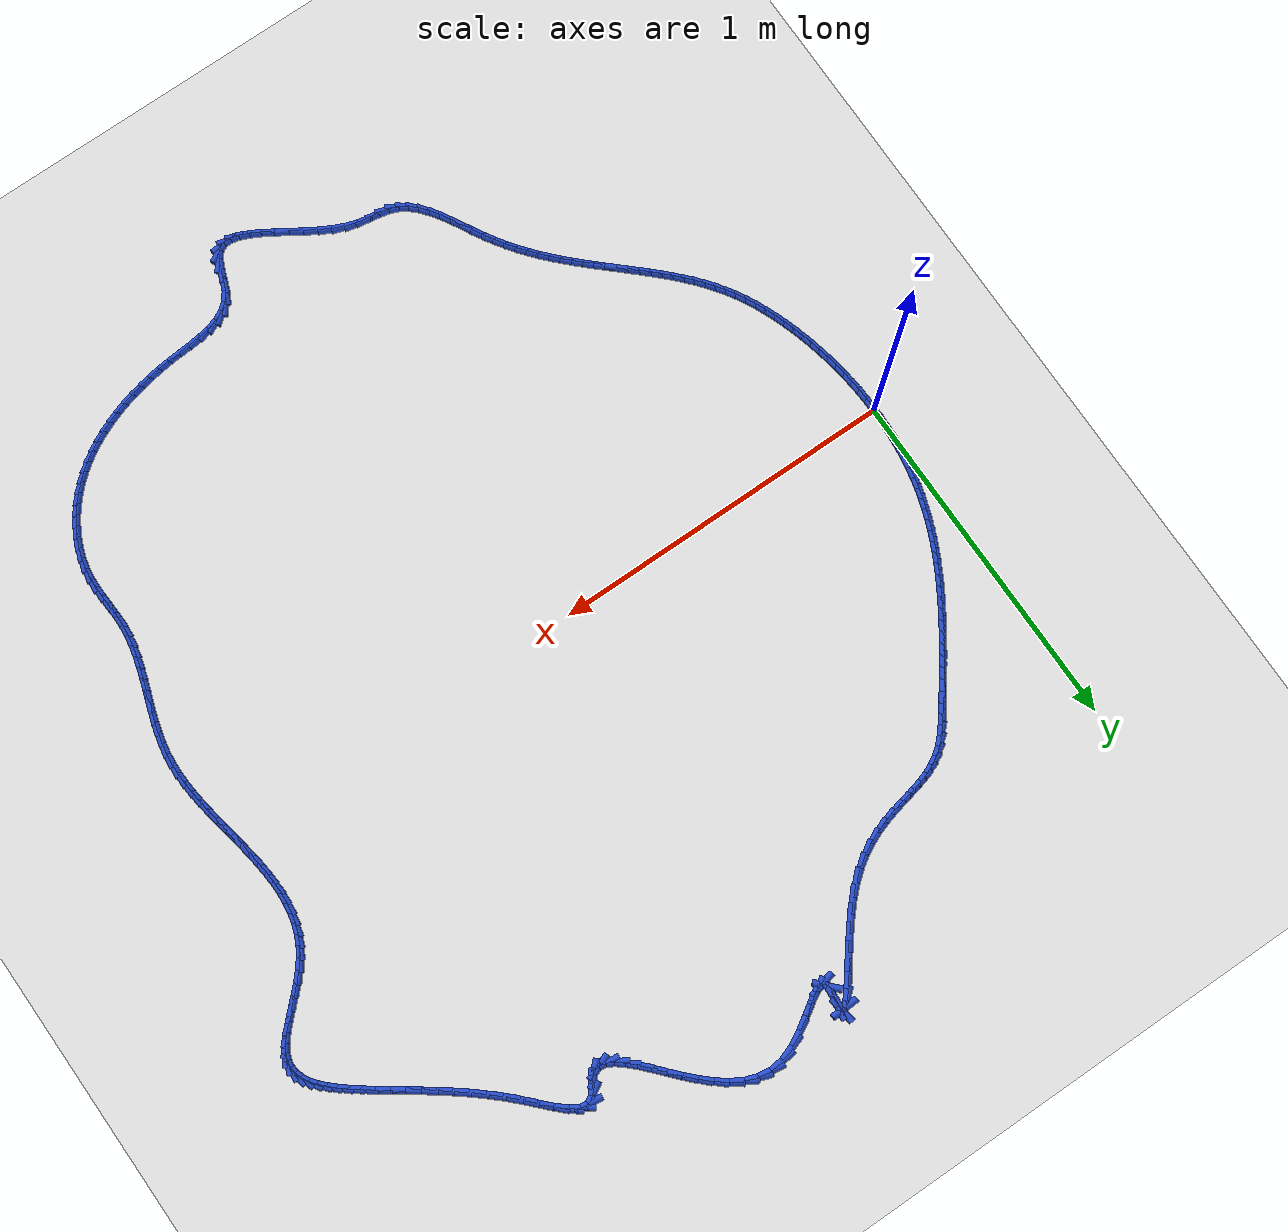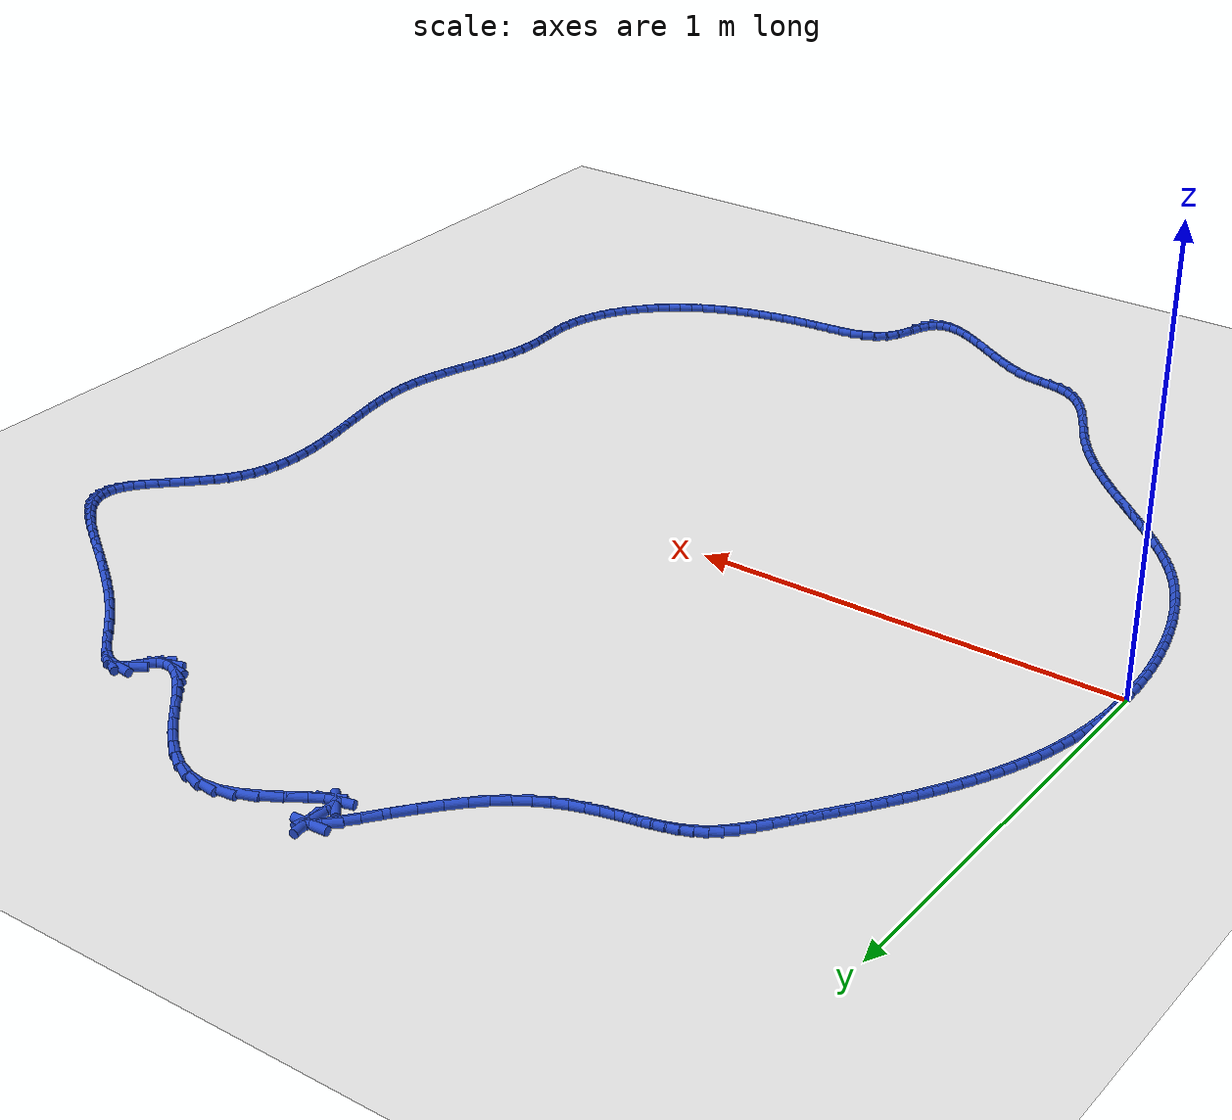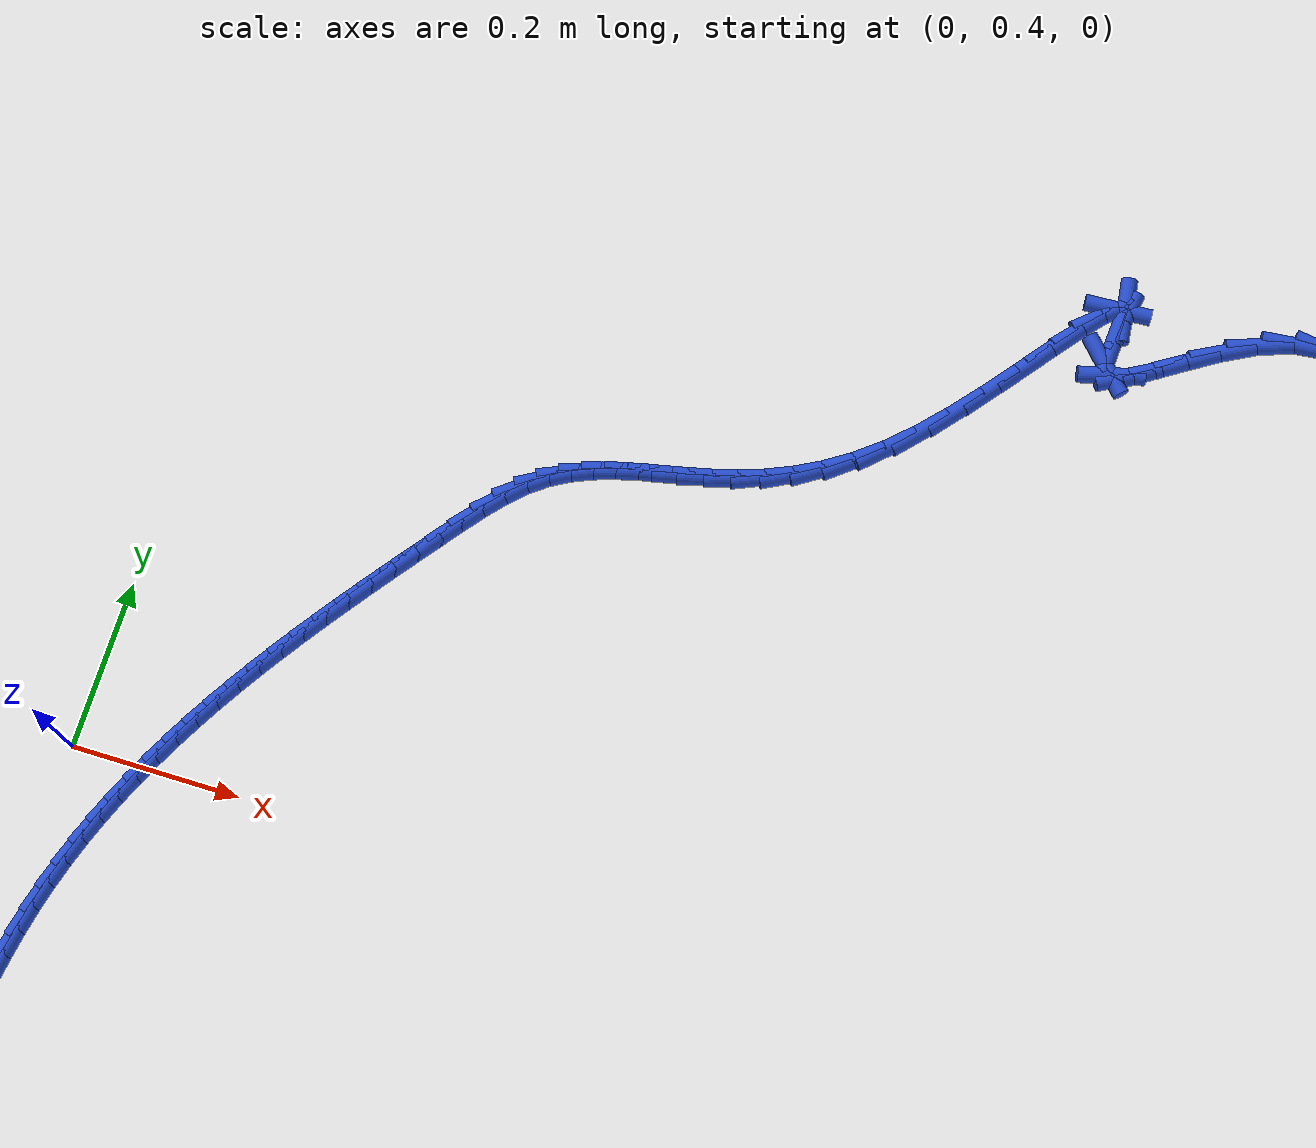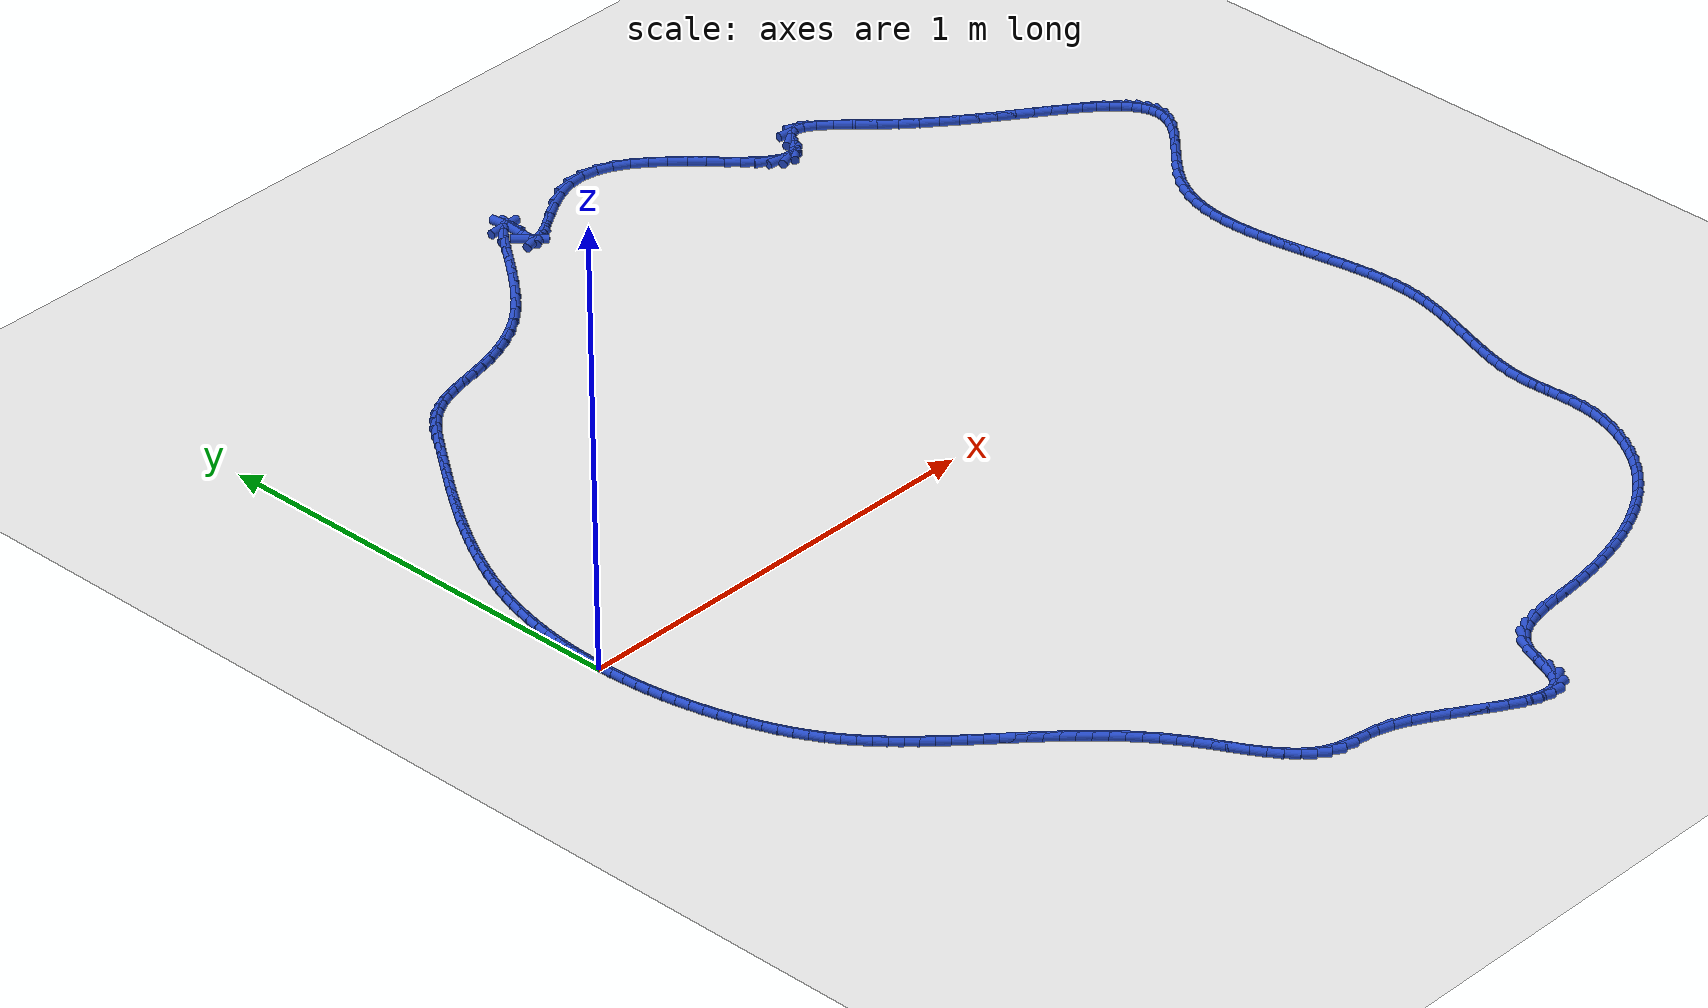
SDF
<sdf version="1.6">
 <world name="default">
  <light name="sun" type="directional">
   <pose>0 0 10 0 -0 0</pose>
   <diffuse>0.8 0.8 0.8 1</diffuse>
   <specular>0.2 0.2 0.2 1</specular>
   <attenuation>
    <range>1000</range>
    <constant>0.9</constant>
    <linear>0.01</linear>
    <quadratic>0.001</quadratic>
   </attenuation>
   <direction>-0.5 0.1 -0.9</direction>
  </light>
  <model name="ground_plane">
   <static>1</static>
   <link name="link">
    <collision name="collision">
     <geometry><plane><normal>0 0 1</normal><size>100 100</size></plane></geometry>
     <surface><friction><ode><mu>100</mu><mu2>50</mu2></ode></friction></surface>
    </collision>
    <visual name="visual">
     <cast_shadows>0</cast_shadows>
     <geometry><plane><normal>0 0 1</normal><size>100 100</size></plane></geometry>
     <material>
      <script><uri>file://media/materials/scripts/gazebo.material</uri><name>Gazebo/WhiteGlow</name></script>
     </material>
    </visual>
   </link>
  </model>
  <gravity>0 0 -9.8</gravity>
  <magnetic_field>6e-06 2.3e-05 -4.2e-05</magnetic_field>
  <atmosphere type="adiabatic"/>
  <physics name="default_physics" default="0" type="ode">
   <max_step_size>0.001</max_step_size>
   <real_time_factor>1</real_time_factor>
   <real_time_update_rate>1000</real_time_update_rate>
  </physics>
  <scene><ambient>0.4 0.4 0.4 1</ambient><background>0.7 0.7 0.7 1</background><shadows>1</shadows></scene>
  <spherical_coordinates>
   <surface_model>EARTH_WGS84</surface_model>
   <latitude_deg>0</latitude_deg>
   <longitude_deg>0</longitude_deg>
   <elevation>0</elevation>
   <heading_deg>0</heading_deg>
  </spherical_coordinates>
  <model name="line">
   <link name="link_0">
    <pose>6.071532165918825e-18 -6.938893903907228e-18 0.01 0 1.57 1.5606146225665916</pose>
    <collision name="collision">
     <geometry><cylinder><radius>0.01</radius><length>0.08</length></cylinder></geometry>
    </collision>
    <visual name="visual">
     <material>
      <script><name>Gazebo/Blue</name><uri>file://media/materials/scripts/gazebo.material</uri></script>
     </material>
     <geometry><cylinder><radius>0.01</radius><length>0.08</length></cylinder></geometry>
    </visual>
   </link>
   <link name="link_1">
    <pose>0.0003144030365966961 0.030878148201406337 0.01 0 1.57 1.5298283075241172</pose>
    <collision name="collision">
     <geometry><cylinder><radius>0.01</radius><length>0.08</length></cylinder></geometry>
    </collision>
    <visual name="visual">
     <material>
      <script><name>Gazebo/Blue</name><uri>file://media/materials/scripts/gazebo.material</uri></script>
     </material>
     <geometry><cylinder><radius>0.01</radius><length>0.08</length></cylinder></geometry>
    </visual>
   </link>
   <link name="link_2">
    <pose>0.0015812782927270923 0.06178436319322704 0.01 0 1.57 1.4984571761689256</pose>
    <collision name="collision">
     <geometry><cylinder><radius>0.01</radius><length>0.08</length></cylinder></geometry>
    </collision>
    <visual name="visual">
     <material>
      <script><name>Gazebo/Blue</name><uri>file://media/materials/scripts/gazebo.material</uri></script>
     </material>
     <geometry><cylinder><radius>0.01</radius><length>0.08</length></cylinder></geometry>
    </visual>
   </link>
   <link name="link_3">
    <pose>0.003818093401102756 0.09265163231806146 0.01 0 1.57 1.466363432714938</pose>
    <collision name="collision">
     <geometry><cylinder><radius>0.01</radius><length>0.08</length></cylinder></geometry>
    </collision>
    <visual name="visual">
     <material>
      <script><name>Gazebo/Blue</name><uri>file://media/materials/scripts/gazebo.material</uri></script>
     </material>
     <geometry><cylinder><radius>0.01</radius><length>0.08</length></cylinder></geometry>
    </visual>
   </link>
   <link name="link_4">
    <pose>0.0070423159944352585 0.12341294291850904 0.01 0 1.57 1.4334088218116157</pose>
    <collision name="collision">
     <geometry><cylinder><radius>0.01</radius><length>0.08</length></cylinder></geometry>
    </collision>
    <visual name="visual">
     <material>
      <script><name>Gazebo/Blue</name><uri>file://media/materials/scripts/gazebo.material</uri></script>
     </material>
     <geometry><cylinder><radius>0.01</radius><length>0.08</length></cylinder></geometry>
    </visual>
   </link>
   <link name="link_5">
    <pose>0.011271413705436162 0.15400128233716914 0.01 0 1.57 1.3994542971568273</pose>
    <collision name="collision">
     <geometry><cylinder><radius>0.01</radius><length>0.08</length></cylinder></geometry>
    </collision>
    <visual name="visual">
     <material>
      <script><name>Gazebo/Blue</name><uri>file://media/materials/scripts/gazebo.material</uri></script>
     </material>
     <geometry><cylinder><radius>0.01</radius><length>0.08</length></cylinder></geometry>
    </visual>
   </link>
   <link name="link_6">
    <pose>0.016522854166817015 0.18434963791664105 0.01 0 1.57 1.3643600368888436</pose>
    <collision name="collision">
     <geometry><cylinder><radius>0.01</radius><length>0.08</length></cylinder></geometry>
    </collision>
    <visual name="visual">
     <material>
      <script><name>Gazebo/Blue</name><uri>file://media/materials/scripts/gazebo.material</uri></script>
     </material>
     <geometry><cylinder><radius>0.01</radius><length>0.08</length></cylinder></geometry>
    </visual>
   </link>
   <link name="link_7">
    <pose>0.0228141050112894 0.21439099699952424 0.01 0 1.57 1.3279858794346828</pose>
    <collision name="collision">
     <geometry><cylinder><radius>0.01</radius><length>0.08</length></cylinder></geometry>
    </collision>
    <visual name="visual">
     <material>
      <script><name>Gazebo/Blue</name><uri>file://media/materials/scripts/gazebo.material</uri></script>
     </material>
     <geometry><cylinder><radius>0.01</radius><length>0.08</length></cylinder></geometry>
    </visual>
   </link>
   <link name="link_8">
    <pose>0.030162633871564877 0.24405834692841805 0.01 0 1.57 1.290490744947438</pose>
    <collision name="collision">
     <geometry><cylinder><radius>0.01</radius><length>0.08</length></cylinder></geometry>
    </collision>
    <visual name="visual">
     <material>
      <script><name>Gazebo/Blue</name><uri>file://media/materials/scripts/gazebo.material</uri></script>
     </material>
     <geometry><cylinder><radius>0.01</radius><length>0.08</length></cylinder></geometry>
    </visual>
   </link>
   <link name="link_9">
    <pose>0.03857912483602734 0.27329392706162275 0.01 0 1.57 1.2537584870091076</pose>
    <collision name="collision">
     <geometry><cylinder><radius>0.01</radius><length>0.08</length></cylinder></geometry>
    </collision>
    <visual name="visual">
     <material>
      <script><name>Gazebo/Blue</name><uri>file://media/materials/scripts/gazebo.material</uri></script>
     </material>
     <geometry><cylinder><radius>0.01</radius><length>0.08</length></cylinder></geometry>
    </visual>
   </link>
   <link name="link_10">
    <pose>0.0480304554355792 0.3020997241310881 0.01 0 1.57 1.2186791028543185</pose>
    <collision name="collision">
     <geometry><cylinder><radius>0.01</radius><length>0.08</length></cylinder></geometry>
    </collision>
    <visual name="visual">
     <material>
      <script><name>Gazebo/Blue</name><uri>file://media/materials/scripts/gazebo.material</uri></script>
     </material>
     <geometry><cylinder><radius>0.01</radius><length>0.08</length></cylinder></geometry>
    </visual>
   </link>
   <link name="link_11">
    <pose>0.05846609784647454 0.3305014638769742 0.01 0 1.57 1.1853778377418578</pose>
    <collision name="collision">
     <geometry><cylinder><radius>0.01</radius><length>0.08</length></cylinder></geometry>
    </collision>
    <visual name="visual">
     <material>
      <script><name>Gazebo/Blue</name><uri>file://media/materials/scripts/gazebo.material</uri></script>
     </material>
     <geometry><cylinder><radius>0.01</radius><length>0.08</length></cylinder></geometry>
    </visual>
   </link>
   <link name="link_12">
    <pose>0.06983548001408091 0.3585249323655527 0.01 0 1.57 1.1539509115376119</pose>
    <collision name="collision">
     <geometry><cylinder><radius>0.01</radius><length>0.08</length></cylinder></geometry>
    </collision>
    <visual name="visual">
     <material>
      <script><name>Gazebo/Blue</name><uri>file://media/materials/scripts/gazebo.material</uri></script>
     </material>
     <geometry><cylinder><radius>0.01</radius><length>0.08</length></cylinder></geometry>
    </visual>
   </link>
   <link name="link_13">
    <pose>0.08208802988376587 0.3861959156630955 0.01 0 1.57 1.124469234404962</pose>
    <collision name="collision">
     <geometry><cylinder><radius>0.01</radius><length>0.08</length></cylinder></geometry>
    </collision>
    <visual name="visual">
     <material>
      <script><name>Gazebo/Blue</name><uri>file://media/materials/scripts/gazebo.material</uri></script>
     </material>
     <geometry><cylinder><radius>0.01</radius><length>0.08</length></cylinder></geometry>
    </visual>
   </link>
   <link name="link_14">
    <pose>0.09517317540089694 0.4135401998358744 0.01 0 1.57 1.0969808955151306</pose>
    <collision name="collision">
     <geometry><cylinder><radius>0.01</radius><length>0.08</length></cylinder></geometry>
    </collision>
    <visual name="visual">
     <material>
      <script><name>Gazebo/Blue</name><uri>file://media/materials/scripts/gazebo.material</uri></script>
     </material>
     <geometry><cylinder><radius>0.01</radius><length>0.08</length></cylinder></geometry>
    </visual>
   </link>
   <link name="link_15">
    <pose>0.10904034451084174 0.44058357095016143 0.01 0 1.57 1.0715140942981298</pose>
    <collision name="collision">
     <geometry><cylinder><radius>0.01</radius><length>0.08</length></cylinder></geometry>
    </collision>
    <visual name="visual">
     <material>
      <script><name>Gazebo/Blue</name><uri>file://media/materials/scripts/gazebo.material</uri></script>
     </material>
     <geometry><cylinder><radius>0.01</radius><length>0.08</length></cylinder></geometry>
    </visual>
   </link>
   <link name="link_16">
    <pose>0.12363896515896779 0.46735181507222845 0.01 0 1.57 1.0480802703301089</pose>
    <collision name="collision">
     <geometry><cylinder><radius>0.01</radius><length>0.08</length></cylinder></geometry>
    </collision>
    <visual name="visual">
     <material>
      <script><name>Gazebo/Blue</name><uri>file://media/materials/scripts/gazebo.material</uri></script>
     </material>
     <geometry><cylinder><radius>0.01</radius><length>0.08</length></cylinder></geometry>
    </visual>
   </link>
   <link name="link_17">
    <pose>0.1389184652906427 0.4938707182683474 0.01 0 1.57 1.0266772340957346</pose>
    <collision name="collision">
     <geometry><cylinder><radius>0.01</radius><length>0.08</length></cylinder></geometry>
    </collision>
    <visual name="visual">
     <material>
      <script><name>Gazebo/Blue</name><uri>file://media/materials/scripts/gazebo.material</uri></script>
     </material>
     <geometry><cylinder><radius>0.01</radius><length>0.08</length></cylinder></geometry>
    </visual>
   </link>
   <link name="link_18">
    <pose>0.154828272851234 0.5201660666047899 0.01 0 1.57 1.0072921513861022</pose>
    <collision name="collision">
     <geometry><cylinder><radius>0.01</radius><length>0.08</length></cylinder></geometry>
    </collision>
    <visual name="visual">
     <material>
      <script><name>Gazebo/Blue</name><uri>file://media/materials/scripts/gazebo.material</uri></script>
     </material>
     <geometry><cylinder><radius>0.01</radius><length>0.08</length></cylinder></geometry>
    </visual>
   </link>
   <link name="link_19">
    <pose>0.17131781578610913 0.5462636461478281 0.01 0 1.57 0.989904282080531</pose>
    <collision name="collision">
     <geometry><cylinder><radius>0.01</radius><length>0.08</length></cylinder></geometry>
    </collision>
    <visual name="visual">
     <material>
      <script><name>Gazebo/Blue</name><uri>file://media/materials/scripts/gazebo.material</uri></script>
     </material>
     <geometry><cylinder><radius>0.01</radius><length>0.08</length></cylinder></geometry>
    </visual>
   </link>
   <link name="link_20">
    <pose>0.1883365220406359 0.5721892429637337 0.01 0 1.57 0.974487415327446</pose>
    <collision name="collision">
     <geometry><cylinder><radius>0.01</radius><length>0.08</length></cylinder></geometry>
    </collision>
    <visual name="visual">
     <material>
      <script><name>Gazebo/Blue</name><uri>file://media/materials/scripts/gazebo.material</uri></script>
     </material>
     <geometry><cylinder><radius>0.01</radius><length>0.08</length></cylinder></geometry>
    </visual>
   </link>
   <link name="link_21">
    <pose>0.2058338195601817 0.5979686431187788 0.01 0 1.57 0.9610119758175012</pose>
    <collision name="collision">
     <geometry><cylinder><radius>0.01</radius><length>0.08</length></cylinder></geometry>
    </collision>
    <visual name="visual">
     <material>
      <script><name>Gazebo/Blue</name><uri>file://media/materials/scripts/gazebo.material</uri></script>
     </material>
     <geometry><cylinder><radius>0.01</radius><length>0.08</length></cylinder></geometry>
    </visual>
   </link>
   <link name="link_22">
    <pose>0.223759136290114 0.6236276326792349 0.01 0 1.57 0.9494467997457402</pose>
    <collision name="collision">
     <geometry><cylinder><radius>0.01</radius><length>0.08</length></cylinder></geometry>
    </collision>
    <visual name="visual">
     <material>
      <script><name>Gazebo/Blue</name><uri>file://media/materials/scripts/gazebo.material</uri></script>
     </material>
     <geometry><cylinder><radius>0.01</radius><length>0.08</length></cylinder></geometry>
    </visual>
   </link>
   <link name="link_23">
    <pose>0.2420619001758006 0.6491919977113744 0.01 0 1.57 0.9397605950378515</pose>
    <collision name="collision">
     <geometry><cylinder><radius>0.01</radius><length>0.08</length></cylinder></geometry>
    </collision>
    <visual name="visual">
     <material>
      <script><name>Gazebo/Blue</name><uri>file://media/materials/scripts/gazebo.material</uri></script>
     </material>
     <geometry><cylinder><radius>0.01</radius><length>0.08</length></cylinder></geometry>
    </visual>
   </link>
   <link name="link_24">
    <pose>0.260691539162609 0.6746875242814689 0.01 0 1.57 0.9319231098250029</pose>
    <collision name="collision">
     <geometry><cylinder><radius>0.01</radius><length>0.08</length></cylinder></geometry>
    </collision>
    <visual name="visual">
     <material>
      <script><name>Gazebo/Blue</name><uri>file://media/materials/scripts/gazebo.material</uri></script>
     </material>
     <geometry><cylinder><radius>0.01</radius><length>0.08</length></cylinder></geometry>
    </visual>
   </link>
   <link name="link_25">
    <pose>0.27959748119590666 0.7001399984557903 0.01 0 1.57 0.9259060374786907</pose>
    <collision name="collision">
     <geometry><cylinder><radius>0.01</radius><length>0.08</length></cylinder></geometry>
    </collision>
    <visual name="visual">
     <material>
      <script><name>Gazebo/Blue</name><uri>file://media/materials/scripts/gazebo.material</uri></script>
     </material>
     <geometry><cylinder><radius>0.01</radius><length>0.08</length></cylinder></geometry>
    </visual>
   </link>
   <link name="link_26">
    <pose>0.29872915422106117 0.7255752063006103 0.01 0 1.57 0.9216836871526607</pose>
    <collision name="collision">
     <geometry><cylinder><radius>0.01</radius><length>0.08</length></cylinder></geometry>
    </collision>
    <visual name="visual">
     <material>
      <script><name>Gazebo/Blue</name><uri>file://media/materials/scripts/gazebo.material</uri></script>
     </material>
     <geometry><cylinder><radius>0.01</radius><length>0.08</length></cylinder></geometry>
    </visual>
   </link>
   <link name="link_27">
    <pose>0.31803598618343987 0.7510189338822008 0.01 0 1.57 0.9189901971206051</pose>
    <collision name="collision">
     <geometry><cylinder><radius>0.01</radius><length>0.08</length></cylinder></geometry>
    </collision>
    <visual name="visual">
     <material>
      <script><name>Gazebo/Blue</name><uri>file://media/materials/scripts/gazebo.material</uri></script>
     </material>
     <geometry><cylinder><radius>0.01</radius><length>0.08</length></cylinder></geometry>
    </visual>
   </link>
   <link name="link_28">
    <pose>0.33747000487616874 0.7764875257632144 0.01 0 1.57 0.9051188082044218</pose>
    <collision name="collision">
     <geometry><cylinder><radius>0.01</radius><length>0.08</length></cylinder></geometry>
    </collision>
    <visual name="visual">
     <material>
      <script><name>Gazebo/Blue</name><uri>file://media/materials/scripts/gazebo.material</uri></script>
     </material>
     <geometry><cylinder><radius>0.01</radius><length>0.08</length></cylinder></geometry>
    </visual>
   </link>
   <link name="link_29">
    <pose>0.3571177642959332 0.8015087865008468 0.01 0 1.57 0.8597161416537701</pose>
    <collision name="collision">
     <geometry><cylinder><radius>0.01</radius><length>0.08</length></cylinder></geometry>
    </collision>
    <visual name="visual">
     <material>
      <script><name>Gazebo/Blue</name><uri>file://media/materials/scripts/gazebo.material</uri></script>
     </material>
     <geometry><cylinder><radius>0.01</radius><length>0.08</length></cylinder></geometry>
    </visual>
   </link>
   <link name="link_30">
    <pose>0.3772628477189194 0.8248949969644558 0.01 0 1.57 0.77490003786797</pose>
    <collision name="collision">
     <geometry><cylinder><radius>0.01</radius><length>0.08</length></cylinder></geometry>
    </collision>
    <visual name="visual">
     <material>
      <script><name>Gazebo/Blue</name><uri>file://media/materials/scripts/gazebo.material</uri></script>
     </material>
     <geometry><cylinder><radius>0.01</radius><length>0.08</length></cylinder></geometry>
    </visual>
   </link>
   <link name="link_31">
    <pose>0.39820451231698023 0.8454015173278632 0.01 0 1.57 0.6485485014471296</pose>
    <collision name="collision">
     <geometry><cylinder><radius>0.01</radius><length>0.08</length></cylinder></geometry>
    </collision>
    <visual name="visual">
     <material>
      <script><name>Gazebo/Blue</name><uri>file://media/materials/scripts/gazebo.material</uri></script>
     </material>
     <geometry><cylinder><radius>0.01</radius><length>0.08</length></cylinder></geometry>
    </visual>
   </link>
   <link name="link_32">
    <pose>0.4201918787304054 0.8620661070335611 0.01 0 1.57 0.5184713946057818</pose>
    <collision name="collision">
     <geometry><cylinder><radius>0.01</radius><length>0.08</length></cylinder></geometry>
    </collision>
    <visual name="visual">
     <material>
      <script><name>Gazebo/Blue</name><uri>file://media/materials/scripts/gazebo.material</uri></script>
     </material>
     <geometry><cylinder><radius>0.01</radius><length>0.08</length></cylinder></geometry>
    </visual>
   </link>
   <link name="link_33">
    <pose>0.44324469032267944 0.8752185170759016 0.01 0 1.57 0.4056807937807828</pose>
    <collision name="collision">
     <geometry><cylinder><radius>0.01</radius><length>0.08</length></cylinder></geometry>
    </collision>
    <visual name="visual">
     <material>
      <script><name>Gazebo/Blue</name><uri>file://media/materials/scripts/gazebo.material</uri></script>
     </material>
     <geometry><cylinder><radius>0.01</radius><length>0.08</length></cylinder></geometry>
    </visual>
   </link>
   <link name="link_34">
    <pose>0.4673171313430829 0.8855577670310238 0.01 0 1.57 0.31730220325802677</pose>
    <collision name="collision">
     <geometry><cylinder><radius>0.01</radius><length>0.08</length></cylinder></geometry>
    </collision>
    <visual name="visual">
     <material>
      <script><name>Gazebo/Blue</name><uri>file://media/materials/scripts/gazebo.material</uri></script>
     </material>
     <geometry><cylinder><radius>0.01</radius><length>0.08</length></cylinder></geometry>
    </visual>
   </link>
   <link name="link_35">
    <pose>0.4923633808962642 0.8937829054527435 0.01 0 1.57 0.25641433667001556</pose>
    <collision name="collision">
     <geometry><cylinder><radius>0.01</radius><length>0.08</length></cylinder></geometry>
    </collision>
    <visual name="visual">
     <material>
      <script><name>Gazebo/Blue</name><uri>file://media/materials/scripts/gazebo.material</uri></script>
     </material>
     <geometry><cylinder><radius>0.01</radius><length>0.08</length></cylinder></geometry>
    </visual>
   </link>
   <link name="link_36">
    <pose>0.5183376180868722 0.9005929808948773 0.01 0 1.57 0.22313429715837954</pose>
    <collision name="collision">
     <geometry><cylinder><radius>0.01</radius><length>0.08</length></cylinder></geometry>
    </collision>
    <visual name="visual">
     <material>
      <script><name>Gazebo/Blue</name><uri>file://media/materials/scripts/gazebo.material</uri></script>
     </material>
     <geometry><cylinder><radius>0.01</radius><length>0.08</length></cylinder></geometry>
    </visual>
   </link>
   <link name="link_37">
    <pose>0.5451940220195554 0.9066870419112412 0.01 0 1.57 0.21602292095242784</pose>
    <collision name="collision">
     <geometry><cylinder><radius>0.01</radius><length>0.08</length></cylinder></geometry>
    </collision>
    <visual name="visual">
     <material>
      <script><name>Gazebo/Blue</name><uri>file://media/materials/scripts/gazebo.material</uri></script>
     </material>
     <geometry><cylinder><radius>0.01</radius><length>0.08</length></cylinder></geometry>
    </visual>
   </link>
   <link name="link_38">
    <pose>0.5728867717989624 0.9127641370556507 0.01 0 1.57 0.23299368610358295</pose>
    <collision name="collision">
     <geometry><cylinder><radius>0.01</radius><length>0.08</length></cylinder></geometry>
    </collision>
    <visual name="visual">
     <material>
      <script><name>Gazebo/Blue</name><uri>file://media/materials/scripts/gazebo.material</uri></script>
     </material>
     <geometry><cylinder><radius>0.01</radius><length>0.08</length></cylinder></geometry>
    </visual>
   </link>
   <link name="link_39">
    <pose>0.6013700465297419 0.9195233148819226 0.01 0 1.57 0.2716272766055668</pose>
    <collision name="collision">
     <geometry><cylinder><radius>0.01</radius><length>0.08</length></cylinder></geometry>
    </collision>
    <visual name="visual">
     <material>
      <script><name>Gazebo/Blue</name><uri>file://media/materials/scripts/gazebo.material</uri></script>
     </material>
     <geometry><cylinder><radius>0.01</radius><length>0.08</length></cylinder></geometry>
    </visual>
   </link>
   <link name="link_40">
    <pose>0.6305980253165426 0.9276636239438728 0.01 0 1.57 0.32909638938551616</pose>
    <collision name="collision">
     <geometry><cylinder><radius>0.01</radius><length>0.08</length></cylinder></geometry>
    </collision>
    <visual name="visual">
     <material>
      <script><name>Gazebo/Blue</name><uri>file://media/materials/scripts/gazebo.material</uri></script>
     </material>
     <geometry><cylinder><radius>0.01</radius><length>0.08</length></cylinder></geometry>
    </visual>
   </link>
   <link name="link_41">
    <pose>0.6605248872640128 0.9378841127953172 0.01 0 1.57 0.4019606466635266</pose>
    <collision name="collision">
     <geometry><cylinder><radius>0.01</radius><length>0.08</length></cylinder></geometry>
    </collision>
    <visual name="visual">
     <material>
      <script><name>Gazebo/Blue</name><uri>file://media/materials/scripts/gazebo.material</uri></script>
     </material>
     <geometry><cylinder><radius>0.01</radius><length>0.08</length></cylinder></geometry>
    </visual>
   </link>
   <link name="link_42">
    <pose>0.6911048114768015 0.9508838299900721 0.01 0 1.57 0.48607593936403165</pose>
    <collision name="collision">
     <geometry><cylinder><radius>0.01</radius><length>0.08</length></cylinder></geometry>
    </collision>
    <visual name="visual">
     <material>
      <script><name>Gazebo/Blue</name><uri>file://media/materials/scripts/gazebo.material</uri></script>
     </material>
     <geometry><cylinder><radius>0.01</radius><length>0.08</length></cylinder></geometry>
    </visual>
   </link>
   <link name="link_43">
    <pose>0.7222919770595572 0.9673618240819537 0.01 0 1.57 0.5767900251005003</pose>
    <collision name="collision">
     <geometry><cylinder><radius>0.01</radius><length>0.08</length></cylinder></geometry>
    </collision>
    <visual name="visual">
     <material>
      <script><name>Gazebo/Blue</name><uri>file://media/materials/scripts/gazebo.material</uri></script>
     </material>
     <geometry><cylinder><radius>0.01</radius><length>0.08</length></cylinder></geometry>
    </visual>
   </link>
   <link name="link_44">
    <pose>0.754040563116928 0.9880171436247775 0.01 0 1.57 0.6694333928839052</pose>
    <collision name="collision">
     <geometry><cylinder><radius>0.01</radius><length>0.08</length></cylinder></geometry>
    </collision>
    <visual name="visual">
     <material>
      <script><name>Gazebo/Blue</name><uri>file://media/materials/scripts/gazebo.material</uri></script>
     </material>
     <geometry><cylinder><radius>0.01</radius><length>0.08</length></cylinder></geometry>
    </visual>
   </link>
   <link name="link_45">
    <pose>0.7863047487535633 1.0135488371723604 0.01 0 1.57 0.7595817913945431</pose>
    <collision name="collision">
     <geometry><cylinder><radius>0.01</radius><length>0.08</length></cylinder></geometry>
    </collision>
    <visual name="visual">
     <material>
      <script><name>Gazebo/Blue</name><uri>file://media/materials/scripts/gazebo.material</uri></script>
     </material>
     <geometry><cylinder><radius>0.01</radius><length>0.08</length></cylinder></geometry>
    </visual>
   </link>
   <link name="link_46">
    <pose>0.8190314305761562 1.0446279195994272 0.01 0 1.57 0.832020393626202</pose>
    <collision name="collision">
     <geometry><cylinder><radius>0.01</radius><length>0.08</length></cylinder></geometry>
    </collision>
    <visual name="visual">
     <material>
      <script><name>Gazebo/Blue</name><uri>file://media/materials/scripts/gazebo.material</uri></script>
     </material>
     <geometry><cylinder><radius>0.01</radius><length>0.08</length></cylinder></geometry>
    </visual>
   </link>
   <link name="link_47">
    <pose>0.8518338441374842 1.0806409911515429 0.01 0 1.57 0.8774825774836054</pose>
    <collision name="collision">
     <geometry><cylinder><radius>0.01</radius><length>0.08</length></cylinder></geometry>
    </collision>
    <visual name="visual">
     <material>
      <script><name>Gazebo/Blue</name><uri>file://media/materials/scripts/gazebo.material</uri></script>
     </material>
     <geometry><cylinder><radius>0.01</radius><length>0.08</length></cylinder></geometry>
    </visual>
   </link>
   <link name="link_48">
    <pose>0.8838600375732023 1.1191839320701162 0.01 0 1.57 0.9034594612172229</pose>
    <collision name="collision">
     <geometry><cylinder><radius>0.01</radius><length>0.08</length></cylinder></geometry>
    </collision>
    <visual name="visual">
     <material>
      <script><name>Gazebo/Blue</name><uri>file://media/materials/scripts/gazebo.material</uri></script>
     </material>
     <geometry><cylinder><radius>0.01</radius><length>0.08</length></cylinder></geometry>
    </visual>
   </link>
   <link name="link_49">
    <pose>0.9142235572158856 1.1577198093116767 0.01 0 1.57 0.912864501387793</pose>
    <collision name="collision">
     <geometry><cylinder><radius>0.01</radius><length>0.08</length></cylinder></geometry>
    </collision>
    <visual name="visual">
     <material>
      <script><name>Gazebo/Blue</name><uri>file://media/materials/scripts/gazebo.material</uri></script>
     </material>
     <geometry><cylinder><radius>0.01</radius><length>0.08</length></cylinder></geometry>
    </visual>
   </link>
   <link name="link_50">
    <pose>0.9420379493981104 1.1937116898327538 0.01 0 1.57 0.9029967884187035</pose>
    <collision name="collision">
     <geometry><cylinder><radius>0.01</radius><length>0.08</length></cylinder></geometry>
    </collision>
    <visual name="visual">
     <material>
      <script><name>Gazebo/Blue</name><uri>file://media/materials/scripts/gazebo.material</uri></script>
     </material>
     <geometry><cylinder><radius>0.01</radius><length>0.08</length></cylinder></geometry>
    </visual>
   </link>
   <link name="link_51">
    <pose>0.9664167604524517 1.224622640589876 0.01 0 1.57 0.8599155647145901</pose>
    <collision name="collision">
     <geometry><cylinder><radius>0.01</radius><length>0.08</length></cylinder></geometry>
    </collision>
    <visual name="visual">
     <material>
      <script><name>Gazebo/Blue</name><uri>file://media/materials/scripts/gazebo.material</uri></script>
     </material>
     <geometry><cylinder><radius>0.01</radius><length>0.08</length></cylinder></geometry>
    </visual>
   </link>
   <link name="link_52">
    <pose>0.9864735367114854 1.2479157285395734 0.01 0 1.57 0.7243734689024477</pose>
    <collision name="collision">
     <geometry><cylinder><radius>0.01</radius><length>0.08</length></cylinder></geometry>
    </collision>
    <visual name="visual">
     <material>
      <script><name>Gazebo/Blue</name><uri>file://media/materials/scripts/gazebo.material</uri></script>
     </material>
     <geometry><cylinder><radius>0.01</radius><length>0.08</length></cylinder></geometry>
    </visual>
   </link>
   <link name="link_53">
    <pose>1.0013218245077873 1.2610540206383747 0.01 0 1.57 0.05097209771861916</pose>
    <collision name="collision">
     <geometry><cylinder><radius>0.01</radius><length>0.08</length></cylinder></geometry>
    </collision>
    <visual name="visual">
     <material>
      <script><name>Gazebo/Blue</name><uri>file://media/materials/scripts/gazebo.material</uri></script>
     </material>
     <geometry><cylinder><radius>0.01</radius><length>0.08</length></cylinder></geometry>
    </visual>
   </link>
   <link name="link_54">
    <pose>1.0100751701739328 1.261500583842809 0.01 0 1.57 -1.451494243946697</pose>
    <collision name="collision">
     <geometry><cylinder><radius>0.01</radius><length>0.08</length></cylinder></geometry>
    </collision>
    <visual name="visual">
     <material>
      <script><name>Gazebo/Blue</name><uri>file://media/materials/scripts/gazebo.material</uri></script>
     </material>
     <geometry><cylinder><radius>0.01</radius><length>0.08</length></cylinder></geometry>
    </visual>
   </link>
   <link name="link_55">
    <pose>1.0118471200424977 1.246718485109406 0.01 0 1.57 1.4133061294663467</pose>
    <collision name="collision">
     <geometry><cylinder><radius>0.01</radius><length>0.08</length></cylinder></geometry>
    </collision>
    <visual name="visual">
     <material>
      <script><name>Gazebo/Blue</name><uri>file://media/materials/scripts/gazebo.material</uri></script>
     </material>
     <geometry><cylinder><radius>0.01</radius><length>0.08</length></cylinder></geometry>
    </visual>
   </link>
   <link name="link_56">
    <pose>1.0070901542676762 1.2167637869534886 0.01 0 1.57 1.5041528170533307</pose>
    <collision name="collision">
     <geometry><cylinder><radius>0.01</radius><length>0.08</length></cylinder></geometry>
    </collision>
    <visual name="visual">
     <material>
      <script><name>Gazebo/Blue</name><uri>file://media/materials/scripts/gazebo.material</uri></script>
     </material>
     <geometry><cylinder><radius>0.01</radius><length>0.08</length></cylinder></geometry>
    </visual>
   </link>
   <link name="link_57">
    <pose>1.0052436531778344 1.1890976776781532 0.01 0 1.57 -0.8276141087509942</pose>
    <collision name="collision">
     <geometry><cylinder><radius>0.01</radius><length>0.08</length></cylinder></geometry>
    </collision>
    <visual name="visual">
     <material>
      <script><name>Gazebo/Blue</name><uri>file://media/materials/scripts/gazebo.material</uri></script>
     </material>
     <geometry><cylinder><radius>0.01</radius><length>0.08</length></cylinder></geometry>
    </visual>
   </link>
   <link name="link_58">
    <pose>1.0145503832916996 1.178970018716499 0.01 0 1.57 0.24892030870415183</pose>
    <collision name="collision">
     <geometry><cylinder><radius>0.01</radius><length>0.08</length></cylinder></geometry>
    </collision>
    <visual name="visual">
     <material>
      <script><name>Gazebo/Blue</name><uri>file://media/materials/scripts/gazebo.material</uri></script>
     </material>
     <geometry><cylinder><radius>0.01</radius><length>0.08</length></cylinder></geometry>
    </visual>
   </link>
   <link name="link_59">
    <pose>1.0340022251989207 1.183914524254335 0.01 0 1.57 0.5147857321639768</pose>
    <collision name="collision">
     <geometry><cylinder><radius>0.01</radius><length>0.08</length></cylinder></geometry>
    </collision>
    <visual name="visual">
     <material>
      <script><name>Gazebo/Blue</name><uri>file://media/materials/scripts/gazebo.material</uri></script>
     </material>
     <geometry><cylinder><radius>0.01</radius><length>0.08</length></cylinder></geometry>
    </visual>
   </link>
   <link name="link_60">
    <pose>1.0615692609070304 1.1995080586891178 0.01 0 1.57 0.5752343237194483</pose>
    <collision name="collision">
     <geometry><cylinder><radius>0.01</radius><length>0.08</length></cylinder></geometry>
    </collision>
    <visual name="visual">
     <material>
      <script><name>Gazebo/Blue</name><uri>file://media/materials/scripts/gazebo.material</uri></script>
     </material>
     <geometry><cylinder><radius>0.01</radius><length>0.08</length></cylinder></geometry>
    </visual>
   </link>
   <link name="link_61">
    <pose>1.0952215724235608 1.2213274864183021 0.01 0 1.57 0.5596454457452085</pose>
    <collision name="collision">
     <geometry><cylinder><radius>0.01</radius><length>0.08</length></cylinder></geometry>
    </collision>
    <visual name="visual">
     <material>
      <script><name>Gazebo/Blue</name><uri>file://media/materials/scripts/gazebo.material</uri></script>
     </material>
     <geometry><cylinder><radius>0.01</radius><length>0.08</length></cylinder></geometry>
    </visual>
   </link>
   <link name="link_62">
    <pose>1.1329292417560441 1.244949671839344 0.01 0 1.57 0.48624305096084397</pose>
    <collision name="collision">
     <geometry><cylinder><radius>0.01</radius><length>0.08</length></cylinder></geometry>
    </collision>
    <visual name="visual">
     <material>
      <script><name>Gazebo/Blue</name><uri>file://media/materials/scripts/gazebo.material</uri></script>
     </material>
     <geometry><cylinder><radius>0.01</radius><length>0.08</length></cylinder></geometry>
    </visual>
   </link>
   <link name="link_63">
    <pose>1.1726623509120127 1.265951479349699 0.01 0 1.57 0.3379187475362613</pose>
    <collision name="collision">
     <geometry><cylinder><radius>0.01</radius><length>0.08</length></cylinder></geometry>
    </collision>
    <visual name="visual">
     <material>
      <script><name>Gazebo/Blue</name><uri>file://media/materials/scripts/gazebo.material</uri></script>
     </material>
     <geometry><cylinder><radius>0.01</radius><length>0.08</length></cylinder></geometry>
    </visual>
   </link>
   <link name="link_64">
    <pose>1.212391881355388 1.279912313911078 0.01 0 1.57 0.10249268913008208</pose>
    <collision name="collision">
     <geometry><cylinder><radius>0.01</radius><length>0.08</length></cylinder></geometry>
    </collision>
    <visual name="visual">
     <material>
      <script><name>Gazebo/Blue</name><uri>file://media/materials/scripts/gazebo.material</uri></script>
     </material>
     <geometry><cylinder><radius>0.01</radius><length>0.08</length></cylinder></geometry>
    </visual>
   </link>
   <link name="link_65">
    <pose>1.2505951078275404 1.2838416338136704 0.01 0 1.57 -0.1436800712177673</pose>
    <collision name="collision">
     <geometry><cylinder><radius>0.01</radius><length>0.08</length></cylinder></geometry>
    </collision>
    <visual name="visual">
     <material>
      <script><name>Gazebo/Blue</name><uri>file://media/materials/scripts/gazebo.material</uri></script>
     </material>
     <geometry><cylinder><radius>0.01</radius><length>0.08</length></cylinder></geometry>
    </visual>
   </link>
   <link name="link_66">
    <pose>1.2870987219813668 1.2785603999525585 0.01 0 1.57 -0.3580870850440642</pose>
    <collision name="collision">
     <geometry><cylinder><radius>0.01</radius><length>0.08</length></cylinder></geometry>
    </collision>
    <visual name="visual">
     <material>
      <script><name>Gazebo/Blue</name><uri>file://media/materials/scripts/gazebo.material</uri></script>
     </material>
     <geometry><cylinder><radius>0.01</radius><length>0.08</length></cylinder></geometry>
    </visual>
   </link>
   <link name="link_67">
    <pose>1.3219517854849698 1.2655176696139137 0.01 0 1.57 -0.5271408985628707</pose>
    <collision name="collision">
     <geometry><cylinder><radius>0.01</radius><length>0.08</length></cylinder></geometry>
    </collision>
    <visual name="visual">
     <material>
      <script><name>Gazebo/Blue</name><uri>file://media/materials/scripts/gazebo.material</uri></script>
     </material>
     <geometry><cylinder><radius>0.01</radius><length>0.08</length></cylinder></geometry>
    </visual>
   </link>
   <link name="link_68">
    <pose>1.3552033600064533 1.2461625000839092 0.01 0 1.57 -0.6524090914437022</pose>
    <collision name="collision">
     <geometry><cylinder><radius>0.01</radius><length>0.08</length></cylinder></geometry>
    </collision>
    <visual name="visual">
     <material>
      <script><name>Gazebo/Blue</name><uri>file://media/materials/scripts/gazebo.material</uri></script>
     </material>
     <geometry><cylinder><radius>0.01</radius><length>0.08</length></cylinder></geometry>
    </visual>
   </link>
   <link name="link_69">
    <pose>1.3869025072139194 1.2219439486487162 0.01 0 1.57 -0.7411081937861198</pose>
    <collision name="collision">
     <geometry><cylinder><radius>0.01</radius><length>0.08</length></cylinder></geometry>
    </collision>
    <visual name="visual">
     <material>
      <script><name>Gazebo/Blue</name><uri>file://media/materials/scripts/gazebo.material</uri></script>
     </material>
     <geometry><cylinder><radius>0.01</radius><length>0.08</length></cylinder></geometry>
    </visual>
   </link>
   <link name="link_70">
    <pose>1.4170982887754704 1.1943110725945063 0.01 0 1.57 -0.8000812248342585</pose>
    <collision name="collision">
     <geometry><cylinder><radius>0.01</radius><length>0.08</length></cylinder></geometry>
    </collision>
    <visual name="visual">
     <material>
      <script><name>Gazebo/Blue</name><uri>file://media/materials/scripts/gazebo.material</uri></script>
     </material>
     <geometry><cylinder><radius>0.01</radius><length>0.08</length></cylinder></geometry>
    </visual>
   </link>
   <link name="link_71">
    <pose>1.4458397663592095 1.164712929207453 0.01 0 1.57 -0.8337171769413737</pose>
    <collision name="collision">
     <geometry><cylinder><radius>0.01</radius><length>0.08</length></cylinder></geometry>
    </collision>
    <visual name="visual">
     <material>
      <script><name>Gazebo/Blue</name><uri>file://media/materials/scripts/gazebo.material</uri></script>
     </material>
     <geometry><cylinder><radius>0.01</radius><length>0.08</length></cylinder></geometry>
    </visual>
   </link>
   <link name="link_72">
    <pose>1.4731760016332405 1.1345985757737274 0.01 0 1.57 -0.8433708566133011</pose>
    <collision name="collision">
     <geometry><cylinder><radius>0.01</radius><length>0.08</length></cylinder></geometry>
    </collision>
    <visual name="visual">
     <material>
      <script><name>Gazebo/Blue</name><uri>file://media/materials/scripts/gazebo.material</uri></script>
     </material>
     <geometry><cylinder><radius>0.01</radius><length>0.08</length></cylinder></geometry>
    </visual>
   </link>
   <link name="link_73">
    <pose>1.4991560562656643 1.1054170695795018 0.01 0 1.57 -0.8266911954921412</pose>
    <collision name="collision">
     <geometry><cylinder><radius>0.01</radius><length>0.08</length></cylinder></geometry>
    </collision>
    <visual name="visual">
     <material>
      <script><name>Gazebo/Blue</name><uri>file://media/materials/scripts/gazebo.material</uri></script>
     </material>
     <geometry><cylinder><radius>0.01</radius><length>0.08</length></cylinder></geometry>
    </visual>
   </link>
   <link name="link_74">
    <pose>1.523828991924585 1.0786174679109481 0.01 0 1.57 -0.7757778338628262</pose>
    <collision name="collision">
     <geometry><cylinder><radius>0.01</radius><length>0.08</length></cylinder></geometry>
    </collision>
    <visual name="visual">
     <material>
      <script><name>Gazebo/Blue</name><uri>file://media/materials/scripts/gazebo.material</uri></script>
     </material>
     <geometry><cylinder><radius>0.01</radius><length>0.08</length></cylinder></geometry>
    </visual>
   </link>
   <link name="link_75">
    <pose>1.547243870278105 1.0556488280542384 0.01 0 1.57 -0.6726482017600872</pose>
    <collision name="collision">
     <geometry><cylinder><radius>0.01</radius><length>0.08</length></cylinder></geometry>
    </collision>
    <visual name="visual">
     <material>
      <script><name>Gazebo/Blue</name><uri>file://media/materials/scripts/gazebo.material</uri></script>
     </material>
     <geometry><cylinder><radius>0.01</radius><length>0.08</length></cylinder></geometry>
    </visual>
   </link>
   <link name="link_76">
    <pose>1.5694497529943279 1.0379602072955447 0.01 0 1.57 -0.4801044883233603</pose>
    <collision name="collision">
     <geometry><cylinder><radius>0.01</radius><length>0.08</length></cylinder></geometry>
    </collision>
    <visual name="visual">
     <material>
      <script><name>Gazebo/Blue</name><uri>file://media/materials/scripts/gazebo.material</uri></script>
     </material>
     <geometry><cylinder><radius>0.01</radius><length>0.08</length></cylinder></geometry>
    </visual>
   </link>
   <link name="link_77">
    <pose>1.590495701741355 1.0270006629210393 0.01 0 1.57 -0.13862852482862015</pose>
    <collision name="collision">
     <geometry><cylinder><radius>0.01</radius><length>0.08</length></cylinder></geometry>
    </collision>
    <visual name="visual">
     <material>
      <script><name>Gazebo/Blue</name><uri>file://media/materials/scripts/gazebo.material</uri></script>
     </material>
     <geometry><cylinder><radius>0.01</radius><length>0.08</length></cylinder></geometry>
    </visual>
   </link>
   <link name="link_78">
    <pose>1.6104307781872906 1.0242192522168945 0.01 0 1.57 0.347964666273585</pose>
    <collision name="collision">
     <geometry><cylinder><radius>0.01</radius><length>0.08</length></cylinder></geometry>
    </collision>
    <visual name="visual">
     <material>
      <script><name>Gazebo/Blue</name><uri>file://media/materials/scripts/gazebo.material</uri></script>
     </material>
     <geometry><cylinder><radius>0.01</radius><length>0.08</length></cylinder></geometry>
    </visual>
   </link>
   <link name="link_79">
    <pose>1.6293040440002364 1.0310650324692814 0.01 0 1.57 0.7871172022710609</pose>
    <collision name="collision">
     <geometry><cylinder><radius>0.01</radius><length>0.08</length></cylinder></geometry>
    </collision>
    <visual name="visual">
     <material>
      <script><name>Gazebo/Blue</name><uri>file://media/materials/scripts/gazebo.material</uri></script>
     </material>
     <geometry><cylinder><radius>0.01</radius><length>0.08</length></cylinder></geometry>
    </visual>
   </link>
   <link name="link_80">
    <pose>1.6471645608482957 1.0489870609643732 0.01 0 1.57 0.9598155010798101</pose>
    <collision name="collision">
     <geometry><cylinder><radius>0.01</radius><length>0.08</length></cylinder></geometry>
    </collision>
    <visual name="visual">
     <material>
      <script><name>Gazebo/Blue</name><uri>file://media/materials/scripts/gazebo.material</uri></script>
     </material>
     <geometry><cylinder><radius>0.01</radius><length>0.08</length></cylinder></geometry>
    </visual>
   </link>
   <link name="link_81">
    <pose>1.6647245583183266 1.0740591678278884 0.01 0 1.57 0.5427511859084333</pose>
    <collision name="collision">
     <geometry><cylinder><radius>0.01</radius><length>0.08</length></cylinder></geometry>
    </collision>
    <visual name="visual">
     <material>
      <script><name>Gazebo/Blue</name><uri>file://media/materials/scripts/gazebo.material</uri></script>
     </material>
     <geometry><cylinder><radius>0.01</radius><length>0.08</length></cylinder></geometry>
    </visual>
   </link>
   <link name="link_82">
    <pose>1.684676513578272 1.0860936992326242 0.01 0 1.57 -0.14173220585602372</pose>
    <collision name="collision">
     <geometry><cylinder><radius>0.01</radius><length>0.08</length></cylinder></geometry>
    </collision>
    <visual name="visual">
     <material>
      <script><name>Gazebo/Blue</name><uri>file://media/materials/scripts/gazebo.material</uri></script>
     </material>
     <geometry><cylinder><radius>0.01</radius><length>0.08</length></cylinder></geometry>
    </visual>
   </link>
   <link name="link_83">
    <pose>1.707404347481935 1.0828506888451315 0.01 0 1.57 -0.5462294685490673</pose>
    <collision name="collision">
     <geometry><cylinder><radius>0.01</radius><length>0.08</length></cylinder></geometry>
    </collision>
    <visual name="visual">
     <material>
      <script><name>Gazebo/Blue</name><uri>file://media/materials/scripts/gazebo.material</uri></script>
     </material>
     <geometry><cylinder><radius>0.01</radius><length>0.08</length></cylinder></geometry>
    </visual>
   </link>
   <link name="link_84">
    <pose>1.732598989299024 1.0675341281983755 0.01 0 1.57 -0.7240404344120058</pose>
    <collision name="collision">
     <geometry><cylinder><radius>0.01</radius><length>0.08</length></cylinder></geometry>
    </collision>
    <visual name="visual">
     <material>
      <script><name>Gazebo/Blue</name><uri>file://media/materials/scripts/gazebo.material</uri></script>
     </material>
     <geometry><cylinder><radius>0.01</radius><length>0.08</length></cylinder></geometry>
    </visual>
   </link>
   <link name="link_85">
    <pose>1.759951368299248 1.0433480088253215 0.01 0 1.57 -0.796415685612915</pose>
    <collision name="collision">
     <geometry><cylinder><radius>0.01</radius><length>0.08</length></cylinder></geometry>
    </collision>
    <visual name="visual">
     <material>
      <script><name>Gazebo/Blue</name><uri>file://media/materials/scripts/gazebo.material</uri></script>
     </material>
     <geometry><cylinder><radius>0.01</radius><length>0.08</length></cylinder></geometry>
    </visual>
   </link>
   <link name="link_86">
    <pose>1.7891524137523158 1.013496322258936 0.01 0 1.57 -0.8103338930790904</pose>
    <collision name="collision">
     <geometry><cylinder><radius>0.01</radius><length>0.08</length></cylinder></geometry>
    </collision>
    <visual name="visual">
     <material>
      <script><name>Gazebo/Blue</name><uri>file://media/materials/scripts/gazebo.material</uri></script>
     </material>
     <geometry><cylinder><radius>0.01</radius><length>0.08</length></cylinder></geometry>
    </visual>
   </link>
   <link name="link_87">
    <pose>1.819893054927938 0.9811830600321843 0.01 0 1.57 -0.7816829093061172</pose>
    <collision name="collision">
     <geometry><cylinder><radius>0.01</radius><length>0.08</length></cylinder></geometry>
    </collision>
    <visual name="visual">
     <material>
      <script><name>Gazebo/Blue</name><uri>file://media/materials/scripts/gazebo.material</uri></script>
     </material>
     <geometry><cylinder><radius>0.01</radius><length>0.08</length></cylinder></geometry>
    </visual>
   </link>
   <link name="link_88">
    <pose>1.8518630044038014 0.9494497853096056 0.01 0 1.57 -0.7400006414438959</pose>
    <collision name="collision">
     <geometry><cylinder><radius>0.01</radius><length>0.08</length></cylinder></geometry>
    </collision>
    <visual name="visual">
     <material>
      <script><name>Gazebo/Blue</name><uri>file://media/materials/scripts/gazebo.material</uri></script>
     </material>
     <geometry><cylinder><radius>0.01</radius><length>0.08</length></cylinder></geometry>
    </visual>
   </link>
   <link name="link_89">
    <pose>1.8847376986971198 0.9194322073723455 0.01 0 1.57 -0.7040671406728405</pose>
    <collision name="collision">
     <geometry><cylinder><radius>0.01</radius><length>0.08</length></cylinder></geometry>
    </collision>
    <visual name="visual">
     <material>
      <script><name>Gazebo/Blue</name><uri>file://media/materials/scripts/gazebo.material</uri></script>
     </material>
     <geometry><cylinder><radius>0.01</radius><length>0.08</length></cylinder></geometry>
    </visual>
   </link>
   <link name="link_90">
    <pose>1.918183300887299 0.8910280316783156 0.01 0 1.57 -0.6741626524313565</pose>
    <collision name="collision">
     <geometry><cylinder><radius>0.01</radius><length>0.08</length></cylinder></geometry>
    </collision>
    <visual name="visual">
     <material>
      <script><name>Gazebo/Blue</name><uri>file://media/materials/scripts/gazebo.material</uri></script>
     </material>
     <geometry><cylinder><radius>0.01</radius><length>0.08</length></cylinder></geometry>
    </visual>
   </link>
   <link name="link_91">
    <pose>1.9518658166377214 0.864113948648157 0.01 0 1.57 -0.6502925018718085</pose>
    <collision name="collision">
     <geometry><cylinder><radius>0.01</radius><length>0.08</length></cylinder></geometry>
    </collision>
    <visual name="visual">
     <material>
      <script><name>Gazebo/Blue</name><uri>file://media/materials/scripts/gazebo.material</uri></script>
     </material>
     <geometry><cylinder><radius>0.01</radius><length>0.08</length></cylinder></geometry>
    </visual>
   </link>
   <link name="link_92">
    <pose>1.9854512516117677 0.8385666487025109 0.01 0 1.57 -0.6325650117026385</pose>
    <collision name="collision">
     <geometry><cylinder><radius>0.01</radius><length>0.08</length></cylinder></geometry>
    </collision>
    <visual name="visual">
     <material>
      <script><name>Gazebo/Blue</name><uri>file://media/materials/scripts/gazebo.material</uri></script>
     </material>
     <geometry><cylinder><radius>0.01</radius><length>0.08</length></cylinder></geometry>
    </visual>
   </link>
   <link name="link_93">
    <pose>2.018605611472821 0.8142628222620178 0.01 0 1.57 -0.6212393941173474</pose>
    <collision name="collision">
     <geometry><cylinder><radius>0.01</radius><length>0.08</length></cylinder></geometry>
    </collision>
    <visual name="visual">
     <material>
      <script><name>Gazebo/Blue</name><uri>file://media/materials/scripts/gazebo.material</uri></script>
     </material>
     <geometry><cylinder><radius>0.01</radius><length>0.08</length></cylinder></geometry>
    </visual>
   </link>
   <link name="link_94">
    <pose>2.05099490188426 0.7910791597473189 0.01 0 1.57 -0.6167840602642738</pose>
    <collision name="collision">
     <geometry><cylinder><radius>0.01</radius><length>0.08</length></cylinder></geometry>
    </collision>
    <visual name="visual">
     <material>
      <script><name>Gazebo/Blue</name><uri>file://media/materials/scripts/gazebo.material</uri></script>
     </material>
     <geometry><cylinder><radius>0.01</radius><length>0.08</length></cylinder></geometry>
    </visual>
   </link>
   <link name="link_95">
    <pose>2.082285128509469 0.7688923515790556 0.01 0 1.57 -0.6199547820081559</pose>
    <collision name="collision">
     <geometry><cylinder><radius>0.01</radius><length>0.08</length></cylinder></geometry>
    </collision>
    <visual name="visual">
     <material>
      <script><name>Gazebo/Blue</name><uri>file://media/materials/scripts/gazebo.material</uri></script>
     </material>
     <geometry><cylinder><radius>0.01</radius><length>0.08</length></cylinder></geometry>
    </visual>
   </link>
   <link name="link_96">
    <pose>2.112142297011829 0.7475790881778683 0.01 0 1.57 -0.6319058772193467</pose>
    <collision name="collision">
     <geometry><cylinder><radius>0.01</radius><length>0.08</length></cylinder></geometry>
    </collision>
    <visual name="visual">
     <material>
      <script><name>Gazebo/Blue</name><uri>file://media/materials/scripts/gazebo.material</uri></script>
     </material>
     <geometry><cylinder><radius>0.01</radius><length>0.08</length></cylinder></geometry>
    </visual>
   </link>
   <link name="link_97">
    <pose>2.140232413054721 0.7270160599643983 0.01 0 1.57 -0.6543528623648104</pose>
    <collision name="collision">
     <geometry><cylinder><radius>0.01</radius><length>0.08</length></cylinder></geometry>
    </collision>
    <visual name="visual">
     <material>
      <script><name>Gazebo/Blue</name><uri>file://media/materials/scripts/gazebo.material</uri></script>
     </material>
     <geometry><cylinder><radius>0.01</radius><length>0.08</length></cylinder></geometry>
    </visual>
   </link>
   <link name="link_98">
    <pose>2.1662214823015273 0.7070799573592867 0.01 0 1.57 -0.6898104874092436</pose>
    <collision name="collision">
     <geometry><cylinder><radius>0.01</radius><length>0.08</length></cylinder></geometry>
    </collision>
    <visual name="visual">
     <material>
      <script><name>Gazebo/Blue</name><uri>file://media/materials/scripts/gazebo.material</uri></script>
     </material>
     <geometry><cylinder><radius>0.01</radius><length>0.08</length></cylinder></geometry>
    </visual>
   </link>
   <link name="link_99">
    <pose>2.18977551041563 0.6876474707831746 0.01 0 1.57 -0.7419281880681682</pose>
    <collision name="collision">
     <geometry><cylinder><radius>0.01</radius><length>0.08</length></cylinder></geometry>
    </collision>
    <visual name="visual">
     <material>
      <script><name>Gazebo/Blue</name><uri>file://media/materials/scripts/gazebo.material</uri></script>
     </material>
     <geometry><cylinder><radius>0.01</radius><length>0.08</length></cylinder></geometry>
    </visual>
   </link>
   <link name="link_100">
    <pose>2.210560503060409 0.6685952906567028 0.01 0 1.57 -0.8159069921870681</pose>
    <collision name="collision">
     <geometry><cylinder><radius>0.01</radius><length>0.08</length></cylinder></geometry>
    </collision>
    <visual name="visual">
     <material>
      <script><name>Gazebo/Blue</name><uri>file://media/materials/scripts/gazebo.material</uri></script>
     </material>
     <geometry><cylinder><radius>0.01</radius><length>0.08</length></cylinder></geometry>
    </visual>
   </link>
   <link name="link_101">
    <pose>2.2282424658992475 0.6498001074005122 0.01 0 1.57 -0.9188164630438234</pose>
    <collision name="collision">
     <geometry><cylinder><radius>0.01</radius><length>0.08</length></cylinder></geometry>
    </collision>
    <visual name="visual">
     <material>
      <script><name>Gazebo/Blue</name><uri>file://media/materials/scripts/gazebo.material</uri></script>
     </material>
     <geometry><cylinder><radius>0.01</radius><length>0.08</length></cylinder></geometry>
    </visual>
   </link>
   <link name="link_102">
    <pose>2.242487404595527 0.6311386114352442 0.01 0 1.57 -1.0591131375494043</pose>
    <collision name="collision">
     <geometry><cylinder><radius>0.01</radius><length>0.08</length></cylinder></geometry>
    </collision>
    <visual name="visual">
     <material>
      <script><name>Gazebo/Blue</name><uri>file://media/materials/scripts/gazebo.material</uri></script>
     </material>
     <geometry><cylinder><radius>0.01</radius><length>0.08</length></cylinder></geometry>
    </visual>
   </link>
   <link name="link_103">
    <pose>2.252961324812628 0.6124874931815394 0.01 0 1.57 -1.2435771659194674</pose>
    <collision name="collision">
     <geometry><cylinder><radius>0.01</radius><length>0.08</length></cylinder></geometry>
    </collision>
    <visual name="visual">
     <material>
      <script><name>Gazebo/Blue</name><uri>file://media/materials/scripts/gazebo.material</uri></script>
     </material>
     <geometry><cylinder><radius>0.01</radius><length>0.08</length></cylinder></geometry>
    </visual>
   </link>
   <link name="link_104">
    <pose>2.2593302322139337 0.5937234430600391 0.01 0 1.57 -1.4695713449307928</pose>
    <collision name="collision">
     <geometry><cylinder><radius>0.01</radius><length>0.08</length></cylinder></geometry>
    </collision>
    <visual name="visual">
     <material>
      <script><name>Gazebo/Blue</name><uri>file://media/materials/scripts/gazebo.material</uri></script>
     </material>
     <geometry><cylinder><radius>0.01</radius><length>0.08</length></cylinder></geometry>
    </visual>
   </link>
   <link name="link_105">
    <pose>2.261260132462824 0.5747231514913845 0.01 0 1.57 1.4249829995298156</pose>
    <collision name="collision">
     <geometry><cylinder><radius>0.01</radius><length>0.08</length></cylinder></geometry>
    </collision>
    <visual name="visual">
     <material>
      <script><name>Gazebo/Blue</name><uri>file://media/materials/scripts/gazebo.material</uri></script>
     </material>
     <geometry><cylinder><radius>0.01</radius><length>0.08</length></cylinder></geometry>
    </visual>
   </link>
   <link name="link_106">
    <pose>2.2584170312226823 0.5553633088962161 0.01 0 1.57 1.1897246050343935</pose>
    <collision name="collision">
     <geometry><cylinder><radius>0.01</radius><length>0.08</length></cylinder></geometry>
    </collision>
    <visual name="visual">
     <material>
      <script><name>Gazebo/Blue</name><uri>file://media/materials/scripts/gazebo.material</uri></script>
     </material>
     <geometry><cylinder><radius>0.01</radius><length>0.08</length></cylinder></geometry>
    </visual>
   </link>
   <link name="link_107">
    <pose>2.2504669341568886 0.535520605695175 0.01 0 1.57 0.9987901538650716</pose>
    <collision name="collision">
     <geometry><cylinder><radius>0.01</radius><length>0.08</length></cylinder></geometry>
    </collision>
    <visual name="visual">
     <material>
      <script><name>Gazebo/Blue</name><uri>file://media/materials/scripts/gazebo.material</uri></script>
     </material>
     <geometry><cylinder><radius>0.01</radius><length>0.08</length></cylinder></geometry>
    </visual>
   </link>
   <link name="link_108">
    <pose>2.237311254195292 0.5150862673399557 0.01 0 1.57 0.8781624858545988</pose>
    <collision name="collision">
     <geometry><cylinder><radius>0.01</radius><length>0.08</length></cylinder></geometry>
    </collision>
    <visual name="visual">
     <material>
      <script><name>Gazebo/Blue</name><uri>file://media/materials/scripts/gazebo.material</uri></script>
     </material>
     <geometry><cylinder><radius>0.01</radius><length>0.08</length></cylinder></geometry>
    </visual>
   </link>
   <link name="link_109">
    <pose>2.2198240266892286 0.4940115730661108 0.01 0 1.57 0.8102430776469247</pose>
    <collision name="collision">
     <geometry><cylinder><radius>0.01</radius><length>0.08</length></cylinder></geometry>
    </collision>
    <visual name="visual">
     <material>
      <script><name>Gazebo/Blue</name><uri>file://media/materials/scripts/gazebo.material</uri></script>
     </material>
     <geometry><cylinder><radius>0.01</radius><length>0.08</length></cylinder></geometry>
    </visual>
   </link>
   <link name="link_110">
    <pose>2.1991304442731185 0.47226330961226987 0.01 0 1.57 0.7783299637950013</pose>
    <collision name="collision">
     <geometry><cylinder><radius>0.01</radius><length>0.08</length></cylinder></geometry>
    </collision>
    <visual name="visual">
     <material>
      <script><name>Gazebo/Blue</name><uri>file://media/materials/scripts/gazebo.material</uri></script>
     </material>
     <geometry><cylinder><radius>0.01</radius><length>0.08</length></cylinder></geometry>
    </visual>
   </link>
   <link name="link_111">
    <pose>2.176355699887241 0.44980826373594696 0.01 0 1.57 0.7739833527305716</pose>
    <collision name="collision">
     <geometry><cylinder><radius>0.01</radius><length>0.08</length></cylinder></geometry>
    </collision>
    <visual name="visual">
     <material>
      <script><name>Gazebo/Blue</name><uri>file://media/materials/scripts/gazebo.material</uri></script>
     </material>
     <geometry><cylinder><radius>0.01</radius><length>0.08</length></cylinder></geometry>
    </visual>
   </link>
   <link name="link_112">
    <pose>2.1526249864718774 0.42661322219465636 0.01 0 1.57 0.7939559845560304</pose>
    <collision name="collision">
     <geometry><cylinder><radius>0.01</radius><length>0.08</length></cylinder></geometry>
    </collision>
    <visual name="visual">
     <material>
      <script><name>Gazebo/Blue</name><uri>file://media/materials/scripts/gazebo.material</uri></script>
     </material>
     <geometry><cylinder><radius>0.01</radius><length>0.08</length></cylinder></geometry>
    </visual>
   </link>
   <link name="link_113">
    <pose>2.129063496967305 0.40264497174591185 0.01 0 1.57 0.838653603792986</pose>
    <collision name="collision">
     <geometry><cylinder><radius>0.01</radius><length>0.08</length></cylinder></geometry>
    </collision>
    <visual name="visual">
     <material>
      <script><name>Gazebo/Blue</name><uri>file://media/materials/scripts/gazebo.material</uri></script>
     </material>
     <geometry><cylinder><radius>0.01</radius><length>0.08</length></cylinder></geometry>
    </visual>
   </link>
   <link name="link_114">
    <pose>2.1067964243138038 0.3778702991472281 0.01 0 1.57 0.9115747017940529</pose>
    <collision name="collision">
     <geometry><cylinder><radius>0.01</radius><length>0.08</length></cylinder></geometry>
    </collision>
    <visual name="visual">
     <material>
      <script><name>Gazebo/Blue</name><uri>file://media/materials/scripts/gazebo.material</uri></script>
     </material>
     <geometry><cylinder><radius>0.01</radius><length>0.08</length></cylinder></geometry>
    </visual>
   </link>
   <link name="link_115">
    <pose>2.086948961451654 0.35225599115611883 0.01 0 1.57 1.015308609664336</pose>
    <collision name="collision">
     <geometry><cylinder><radius>0.01</radius><length>0.08</length></cylinder></geometry>
    </collision>
    <visual name="visual">
     <material>
      <script><name>Gazebo/Blue</name><uri>file://media/materials/scripts/gazebo.material</uri></script>
     </material>
     <geometry><cylinder><radius>0.01</radius><length>0.08</length></cylinder></geometry>
    </visual>
   </link>
   <link name="link_116">
    <pose>2.070514463659539 0.32577783352353673 0.01 0 1.57 1.1283465357218607</pose>
    <collision name="collision">
     <geometry><cylinder><radius>0.01</radius><length>0.08</length></cylinder></geometry>
    </collision>
    <visual name="visual">
     <material>
      <script><name>Gazebo/Blue</name><uri>file://media/materials/scripts/gazebo.material</uri></script>
     </material>
     <geometry><cylinder><radius>0.01</radius><length>0.08</length></cylinder></geometry>
    </visual>
   </link>
   <link name="link_117">
    <pose>2.05757834647514 0.2984735862775333 0.01 0 1.57 1.236937117680018</pose>
    <collision name="collision">
     <geometry><cylinder><radius>0.01</radius><length>0.08</length></cylinder></geometry>
    </collision>
    <visual name="visual">
     <material>
      <script><name>Gazebo/Blue</name><uri>file://media/materials/scripts/gazebo.material</uri></script>
     </material>
     <geometry><cylinder><radius>0.01</radius><length>0.08</length></cylinder></geometry>
    </visual>
   </link>
   <link name="link_118">
    <pose>2.0478436962090063 0.27040710652771116 0.01 0 1.57 1.3376231012405686</pose>
    <collision name="collision">
     <geometry><cylinder><radius>0.01</radius><length>0.08</length></cylinder></geometry>
    </collision>
    <visual name="visual">
     <material>
      <script><name>Gazebo/Blue</name><uri>file://media/materials/scripts/gazebo.material</uri></script>
     </material>
     <geometry><cylinder><radius>0.01</radius><length>0.08</length></cylinder></geometry>
    </visual>
   </link>
   <link name="link_119">
    <pose>2.0410122645471485 0.241642342482661 0.01 0 1.57 1.428013026705768</pose>
    <collision name="collision">
     <geometry><cylinder><radius>0.01</radius><length>0.08</length></cylinder></geometry>
    </collision>
    <visual name="visual">
     <material>
      <script><name>Gazebo/Blue</name><uri>file://media/materials/scripts/gazebo.material</uri></script>
     </material>
     <geometry><cylinder><radius>0.01</radius><length>0.08</length></cylinder></geometry>
    </visual>
   </link>
   <link name="link_120">
    <pose>2.036785803175577 0.21224324235097397 0.01 0 1.57 1.5068272616887632</pose>
    <collision name="collision">
     <geometry><cylinder><radius>0.01</radius><length>0.08</length></cylinder></geometry>
    </collision>
    <visual name="visual">
     <material>
      <script><name>Gazebo/Blue</name><uri>file://media/materials/scripts/gazebo.material</uri></script>
     </material>
     <geometry><cylinder><radius>0.01</radius><length>0.08</length></cylinder></geometry>
    </visual>
   </link>
   <link name="link_121">
    <pose>2.0348660637803007 0.18227375434123957 0.01 0 1.57 -1.5678847167787344</pose>
    <collision name="collision">
     <geometry><cylinder><radius>0.01</radius><length>0.08</length></cylinder></geometry>
    </collision>
    <visual name="visual">
     <material>
      <script><name>Gazebo/Blue</name><uri>file://media/materials/scripts/gazebo.material</uri></script>
     </material>
     <geometry><cylinder><radius>0.01</radius><length>0.08</length></cylinder></geometry>
    </visual>
   </link>
   <link name="link_122">
    <pose>2.034954798047331 0.15179782666204883 0.01 0 1.57 -1.5126777773674571</pose>
    <collision name="collision">
     <geometry><cylinder><radius>0.01</radius><length>0.08</length></cylinder></geometry>
    </collision>
    <visual name="visual">
     <material>
      <script><name>Gazebo/Blue</name><uri>file://media/materials/scripts/gazebo.material</uri></script>
     </material>
     <geometry><cylinder><radius>0.01</radius><length>0.08</length></cylinder></geometry>
    </visual>
   </link>
   <link name="link_123">
    <pose>2.036753757662676 0.12087940752199215 0.01 0 1.57 -1.4685582490516331</pose>
    <collision name="collision">
     <geometry><cylinder><radius>0.01</radius><length>0.08</length></cylinder></geometry>
    </collision>
    <visual name="visual">
     <material>
      <script><name>Gazebo/Blue</name><uri>file://media/materials/scripts/gazebo.material</uri></script>
     </material>
     <geometry><cylinder><radius>0.01</radius><length>0.08</length></cylinder></geometry>
    </visual>
   </link>
   <link name="link_124">
    <pose>2.039964694312347 0.08958244512966015 0.01 0 1.57 -1.4348338958024054</pose>
    <collision name="collision">
     <geometry><cylinder><radius>0.01</radius><length>0.08</length></cylinder></geometry>
    </collision>
    <visual name="visual">
     <material>
      <script><name>Gazebo/Blue</name><uri>file://media/materials/scripts/gazebo.material</uri></script>
     </material>
     <geometry><cylinder><radius>0.01</radius><length>0.08</length></cylinder></geometry>
    </visual>
   </link>
   <link name="link_125">
    <pose>2.044289359682355 0.057970887693643336 0.01 0 1.57 -1.410850149807186</pose>
    <collision name="collision">
     <geometry><cylinder><radius>0.01</radius><length>0.08</length></cylinder></geometry>
    </collision>
    <visual name="visual">
     <material>
      <script><name>Gazebo/Blue</name><uri>file://media/materials/scripts/gazebo.material</uri></script>
     </material>
     <geometry><cylinder><radius>0.01</radius><length>0.08</length></cylinder></geometry>
    </visual>
   </link>
   <link name="link_126">
    <pose>2.0494295054587086 0.026108683422532274 0.01 0 1.57 -1.3960730154741505</pose>
    <collision name="collision">
     <geometry><cylinder><radius>0.01</radius><length>0.08</length></cylinder></geometry>
    </collision>
    <visual name="visual">
     <material>
      <script><name>Gazebo/Blue</name><uri>file://media/materials/scripts/gazebo.material</uri></script>
     </material>
     <geometry><cylinder><radius>0.01</radius><length>0.08</length></cylinder></geometry>
    </visual>
   </link>
   <link name="link_127">
    <pose>2.0550868833274176 -0.00594021947508265 0.01 0 1.57 -1.3901314532919269</pose>
    <collision name="collision">
     <geometry><cylinder><radius>0.01</radius><length>0.08</length></cylinder></geometry>
    </collision>
    <visual name="visual">
     <material>
      <script><name>Gazebo/Blue</name><uri>file://media/materials/scripts/gazebo.material</uri></script>
     </material>
     <geometry><cylinder><radius>0.01</radius><length>0.08</length></cylinder></geometry>
    </visual>
   </link>
   <link name="link_128">
    <pose>2.0609632449744923 -0.03811187279061074 0.01 0 1.57 -1.392835169889218</pose>
    <collision name="collision">
     <geometry><cylinder><radius>0.01</radius><length>0.08</length></cylinder></geometry>
    </collision>
    <visual name="visual">
     <material>
      <script><name>Gazebo/Blue</name><uri>file://media/materials/scripts/gazebo.material</uri></script>
     </material>
     <geometry><cylinder><radius>0.01</radius><length>0.08</length></cylinder></geometry>
    </visual>
   </link>
   <link name="link_129">
    <pose>2.0667603420859435 -0.07034232831546161 0.01 0 1.57 -1.4041776402437252</pose>
    <collision name="collision">
     <geometry><cylinder><radius>0.01</radius><length>0.08</length></cylinder></geometry>
    </collision>
    <visual name="visual">
     <material>
      <script><name>Gazebo/Blue</name><uri>file://media/materials/scripts/gazebo.material</uri></script>
     </material>
     <geometry><cylinder><radius>0.01</radius><length>0.08</length></cylinder></geometry>
    </visual>
   </link>
   <link name="link_130">
    <pose>2.07217992634778 -0.10256763784104465 0.01 0 1.57 -1.4243284783498862</pose>
    <collision name="collision">
     <geometry><cylinder><radius>0.01</radius><length>0.08</length></cylinder></geometry>
    </collision>
    <visual name="visual">
     <material>
      <script><name>Gazebo/Blue</name><uri>file://media/materials/scripts/gazebo.material</uri></script>
     </material>
     <geometry><cylinder><radius>0.01</radius><length>0.08</length></cylinder></geometry>
    </visual>
   </link>
   <link name="link_131">
    <pose>2.0769237494460127 -0.1347238531587694 0.01 0 1.57 -1.4536142296532368</pose>
    <collision name="collision">
     <geometry><cylinder><radius>0.01</radius><length>0.08</length></cylinder></geometry>
    </collision>
    <visual name="visual">
     <material>
      <script><name>Gazebo/Blue</name><uri>file://media/materials/scripts/gazebo.material</uri></script>
     </material>
     <geometry><cylinder><radius>0.01</radius><length>0.08</length></cylinder></geometry>
    </visual>
   </link>
   <link name="link_132">
    <pose>2.0806935630666508 -0.16674702606004527 0.01 0 1.57 -1.4924819451534839</pose>
    <collision name="collision">
     <geometry><cylinder><radius>0.01</radius><length>0.08</length></cylinder></geometry>
    </collision>
    <visual name="visual">
     <material>
      <script><name>Gazebo/Blue</name><uri>file://media/materials/scripts/gazebo.material</uri></script>
     </material>
     <geometry><cylinder><radius>0.01</radius><length>0.08</length></cylinder></geometry>
    </visual>
   </link>
   <link name="link_133">
    <pose>2.083191118895705 -0.19857320833628175 0.01 0 1.57 -1.5414354470463512</pose>
    <collision name="collision">
     <geometry><cylinder><radius>0.01</radius><length>0.08</length></cylinder></geometry>
    </collision>
    <visual name="visual">
     <material>
      <script><name>Gazebo/Blue</name><uri>file://media/materials/scripts/gazebo.material</uri></script>
     </material>
     <geometry><cylinder><radius>0.01</radius><length>0.08</length></cylinder></geometry>
    </visual>
   </link>
   <link name="link_134">
    <pose>2.0841181686191854 -0.23013845177888834 0.01 0 1.57 1.5406615993870583</pose>
    <collision name="collision">
     <geometry><cylinder><radius>0.01</radius><length>0.08</length></cylinder></geometry>
    </collision>
    <visual name="visual">
     <material>
      <script><name>Gazebo/Blue</name><uri>file://media/materials/scripts/gazebo.material</uri></script>
     </material>
     <geometry><cylinder><radius>0.01</radius><length>0.08</length></cylinder></geometry>
    </visual>
   </link>
   <link name="link_135">
    <pose>2.083176463923102 -0.2613788081792746 0.01 0 1.57 1.470783067310562</pose>
    <collision name="collision">
     <geometry><cylinder><radius>0.01</radius><length>0.08</length></cylinder></geometry>
    </collision>
    <visual name="visual">
     <material>
      <script><name>Gazebo/Blue</name><uri>file://media/materials/scripts/gazebo.material</uri></script>
     </material>
     <geometry><cylinder><radius>0.01</radius><length>0.08</length></cylinder></geometry>
    </visual>
   </link>
   <link name="link_136">
    <pose>2.080080343876967 -0.292232617307837 0.01 0 1.57 1.4012558245433664</pose>
    <collision name="collision">
     <geometry><cylinder><radius>0.01</radius><length>0.08</length></cylinder></geometry>
    </collision>
    <visual name="visual">
     <material>
      <script><name>Gazebo/Blue</name><uri>file://media/materials/scripts/gazebo.material</uri></script>
     </material>
     <geometry><cylinder><radius>0.01</radius><length>0.08</length></cylinder></geometry>
    </visual>
   </link>
   <link name="link_137">
    <pose>2.0748654007649976 -0.3226966123734996 0.01 0 1.57 1.343854834736413</pose>
    <collision name="collision">
     <geometry><cylinder><radius>0.01</radius><length>0.08</length></cylinder></geometry>
    </collision>
    <visual name="visual">
     <material>
      <script><name>Gazebo/Blue</name><uri>file://media/materials/scripts/gazebo.material</uri></script>
     </material>
     <geometry><cylinder><radius>0.01</radius><length>0.08</length></cylinder></geometry>
    </visual>
   </link>
   <link name="link_138">
    <pose>2.0679071722468185 -0.35282931765364284 0.01 0 1.57 1.2994020416662242</pose>
    <collision name="collision">
     <geometry><cylinder><radius>0.01</radius><length>0.08</length></cylinder></geometry>
    </collision>
    <visual name="visual">
     <material>
      <script><name>Gazebo/Blue</name><uri>file://media/materials/scripts/gazebo.material</uri></script>
     </material>
     <geometry><cylinder><radius>0.01</radius><length>0.08</length></cylinder></geometry>
    </visual>
   </link>
   <link name="link_139">
    <pose>2.0595975255465055 -0.3826922256120318 0.01 0 1.57 1.2678458943947435</pose>
    <collision name="collision">
     <geometry><cylinder><radius>0.01</radius><length>0.08</length></cylinder></geometry>
    </collision>
    <visual name="visual">
     <material>
      <script><name>Gazebo/Blue</name><uri>file://media/materials/scripts/gazebo.material</uri></script>
     </material>
     <geometry><cylinder><radius>0.01</radius><length>0.08</length></cylinder></geometry>
    </visual>
   </link>
   <link name="link_140">
    <pose>2.0503283278881366 -0.4123468287124319 0.01 0 1.57 1.2490167619924768</pose>
    <collision name="collision">
     <geometry><cylinder><radius>0.01</radius><length>0.08</length></cylinder></geometry>
    </collision>
    <visual name="visual">
     <material>
      <script><name>Gazebo/Blue</name><uri>file://media/materials/scripts/gazebo.material</uri></script>
     </material>
     <geometry><cylinder><radius>0.01</radius><length>0.08</length></cylinder></geometry>
    </visual>
   </link>
   <link name="link_141">
    <pose>2.0404914464957886 -0.4418546194186082 0.01 0 1.57 1.242781891761491</pose>
    <collision name="collision">
     <geometry><cylinder><radius>0.01</radius><length>0.08</length></cylinder></geometry>
    </collision>
    <visual name="visual">
     <material>
      <script><name>Gazebo/Blue</name><uri>file://media/materials/scripts/gazebo.material</uri></script>
     </material>
     <geometry><cylinder><radius>0.01</radius><length>0.08</length></cylinder></geometry>
    </visual>
   </link>
   <link name="link_142">
    <pose>2.030478748593538 -0.4712770901943263 0.01 0 1.57 1.2491345724383032</pose>
    <collision name="collision">
     <geometry><cylinder><radius>0.01</radius><length>0.08</length></cylinder></geometry>
    </collision>
    <visual name="visual">
     <material>
      <script><name>Gazebo/Blue</name><uri>file://media/materials/scripts/gazebo.material</uri></script>
     </material>
     <geometry><cylinder><radius>0.01</radius><length>0.08</length></cylinder></geometry>
    </visual>
   </link>
   <link name="link_143">
    <pose>2.0206821014054612 -0.5006757335033513 0.01 0 1.57 1.2682246057039166</pose>
    <collision name="collision">
     <geometry><cylinder><radius>0.01</radius><length>0.08</length></cylinder></geometry>
    </collision>
    <visual name="visual">
     <material>
      <script><name>Gazebo/Blue</name><uri>file://media/materials/scripts/gazebo.material</uri></script>
     </material>
     <geometry><cylinder><radius>0.01</radius><length>0.08</length></cylinder></geometry>
    </visual>
   </link>
   <link name="link_144">
    <pose>2.011493372155636 -0.5301120418094484 0.01 0 1.57 1.3003320880393365</pose>
    <collision name="collision">
     <geometry><cylinder><radius>0.01</radius><length>0.08</length></cylinder></geometry>
    </collision>
    <visual name="visual">
     <material>
      <script><name>Gazebo/Blue</name><uri>file://media/materials/scripts/gazebo.material</uri></script>
     </material>
     <geometry><cylinder><radius>0.01</radius><length>0.08</length></cylinder></geometry>
    </visual>
   </link>
   <link name="link_145">
    <pose>2.0033044280681382 -0.559647507576382 0.01 0 1.57 1.3457776965861095</pose>
    <collision name="collision">
     <geometry><cylinder><radius>0.01</radius><length>0.08</length></cylinder></geometry>
    </collision>
    <visual name="visual">
     <material>
      <script><name>Gazebo/Blue</name><uri>file://media/materials/scripts/gazebo.material</uri></script>
     </material>
     <geometry><cylinder><radius>0.01</radius><length>0.08</length></cylinder></geometry>
    </visual>
   </link>
   <link name="link_146">
    <pose>1.9965071363670455 -0.5893436232679194 0.01 0 1.57 1.4047568437098972</pose>
    <collision name="collision">
     <geometry><cylinder><radius>0.01</radius><length>0.08</length></cylinder></geometry>
    </collision>
    <visual name="visual">
     <material>
      <script><name>Gazebo/Blue</name><uri>file://media/materials/scripts/gazebo.material</uri></script>
     </material>
     <geometry><cylinder><radius>0.01</radius><length>0.08</length></cylinder></geometry>
    </visual>
   </link>
   <link name="link_147">
    <pose>1.9914933642764348 -0.619261881347825 0.01 0 1.57 1.4770911757620213</pose>
    <collision name="collision">
     <geometry><cylinder><radius>0.01</radius><length>0.08</length></cylinder></geometry>
    </collision>
    <visual name="visual">
     <material>
      <script><name>Gazebo/Blue</name><uri>file://media/materials/scripts/gazebo.material</uri></script>
     </material>
     <geometry><cylinder><radius>0.01</radius><length>0.08</length></cylinder></geometry>
    </visual>
   </link>
   <link name="link_148">
    <pose>1.9886549788445207 -0.6494637742586965 0.01 0 1.57 1.5536989346588497</pose>
    <collision name="collision">
     <geometry><cylinder><radius>0.01</radius><length>0.08</length></cylinder></geometry>
    </collision>
    <visual name="visual">
     <material>
      <script><name>Gazebo/Blue</name><uri>file://media/materials/scripts/gazebo.material</uri></script>
     </material>
     <geometry><cylinder><radius>0.01</radius><length>0.08</length></cylinder></geometry>
    </visual>
   </link>
   <link name="link_149">
    <pose>1.9881331694901367 -0.6799806217402059 0.01 0 1.57 -1.5395873241234328</pose>
    <collision name="collision">
     <geometry><cylinder><radius>0.01</radius><length>0.08</length></cylinder></geometry>
    </collision>
    <visual name="visual">
     <material>
      <script><name>Gazebo/Blue</name><uri>file://media/materials/scripts/gazebo.material</uri></script>
     </material>
     <geometry><cylinder><radius>0.01</radius><length>0.08</length></cylinder></geometry>
    </visual>
   </link>
   <link name="link_150">
    <pose>1.9890930217000873 -0.7107262552103186 0.01 0 1.57 -1.5264616736454009</pose>
    <collision name="collision">
     <geometry><cylinder><radius>0.01</radius><length>0.08</length></cylinder></geometry>
    </collision>
    <visual name="visual">
     <material>
      <script><name>Gazebo/Blue</name><uri>file://media/materials/scripts/gazebo.material</uri></script>
     </material>
     <geometry><cylinder><radius>0.01</radius><length>0.08</length></cylinder></geometry>
    </visual>
   </link>
   <link name="link_151">
    <pose>1.990462071047597 -0.7415859134958298 0.01 0 1.57 -1.54792906542039</pose>
    <collision name="collision">
     <geometry><cylinder><radius>0.01</radius><length>0.08</length></cylinder></geometry>
    </collision>
    <visual name="visual">
     <material>
      <script><name>Gazebo/Blue</name><uri>file://media/materials/scripts/gazebo.material</uri></script>
     </material>
     <geometry><cylinder><radius>0.01</radius><length>0.08</length></cylinder></geometry>
    </visual>
   </link>
   <link name="link_152">
    <pose>1.991167853105894 -0.7724448354235346 0.01 0 1.57 1.537307390004728</pose>
    <collision name="collision">
     <geometry><cylinder><radius>0.01</radius><length>0.08</length></cylinder></geometry>
    </collision>
    <visual name="visual">
     <material>
      <script><name>Gazebo/Blue</name><uri>file://media/materials/scripts/gazebo.material</uri></script>
     </material>
     <geometry><cylinder><radius>0.01</radius><length>0.08</length></cylinder></geometry>
    </visual>
   </link>
   <link name="link_153">
    <pose>1.990137903448204 -0.8031882598202287 0.01 0 1.57 1.446440154748231</pose>
    <collision name="collision">
     <geometry><cylinder><radius>0.01</radius><length>0.08</length></cylinder></geometry>
    </collision>
    <visual name="visual">
     <material>
      <script><name>Gazebo/Blue</name><uri>file://media/materials/scripts/gazebo.material</uri></script>
     </material>
     <geometry><cylinder><radius>0.01</radius><length>0.08</length></cylinder></geometry>
    </visual>
   </link>
   <link name="link_154">
    <pose>1.9863239950803202 -0.8336992348590614 0.01 0 1.57 1.3421130693477743</pose>
    <collision name="collision">
     <geometry><cylinder><radius>0.01</radius><length>0.08</length></cylinder></geometry>
    </collision>
    <visual name="visual">
     <material>
      <script><name>Gazebo/Blue</name><uri>file://media/materials/scripts/gazebo.material</uri></script>
     </material>
     <geometry><cylinder><radius>0.01</radius><length>0.08</length></cylinder></geometry>
    </visual>
   </link>
   <link name="link_155">
    <pose>1.9793171910135163 -0.8638030277177279 0.01 0 1.57 1.245981788400404</pose>
    <collision name="collision">
     <geometry><cylinder><radius>0.01</radius><length>0.08</length></cylinder></geometry>
    </collision>
    <visual name="visual">
     <material>
      <script><name>Gazebo/Blue</name><uri>file://media/materials/scripts/gazebo.material</uri></script>
     </material>
     <geometry><cylinder><radius>0.01</radius><length>0.08</length></cylinder></geometry>
    </visual>
   </link>
   <link name="link_156">
    <pose>1.9693969074418611 -0.8932626900977136 0.01 0 1.57 1.157842711658586</pose>
    <collision name="collision">
     <geometry><cylinder><radius>0.01</radius><length>0.08</length></cylinder></geometry>
    </collision>
    <visual name="visual">
     <material>
      <script><name>Gazebo/Blue</name><uri>file://media/materials/scripts/gazebo.material</uri></script>
     </material>
     <geometry><cylinder><radius>0.01</radius><length>0.08</length></cylinder></geometry>
    </visual>
   </link>
   <link name="link_157">
    <pose>1.9568766274495255 -0.9218381946302775 0.01 0 1.57 1.0761403704777643</pose>
    <collision name="collision">
     <geometry><cylinder><radius>0.01</radius><length>0.08</length></cylinder></geometry>
    </collision>
    <visual name="visual">
     <material>
      <script><name>Gazebo/Blue</name><uri>file://media/materials/scripts/gazebo.material</uri></script>
     </material>
     <geometry><cylinder><radius>0.01</radius><length>0.08</length></cylinder></geometry>
    </visual>
   </link>
   <link name="link_158">
    <pose>1.9420698341206806 -0.9492895139466788 0.01 0 1.57 0.9992001105367296</pose>
    <collision name="collision">
     <geometry><cylinder><radius>0.01</radius><length>0.08</length></cylinder></geometry>
    </collision>
    <visual name="visual">
     <material>
      <script><name>Gazebo/Blue</name><uri>file://media/materials/scripts/gazebo.material</uri></script>
     </material>
     <geometry><cylinder><radius>0.01</radius><length>0.08</length></cylinder></geometry>
    </visual>
   </link>
   <link name="link_159">
    <pose>1.9252900105394957 -0.9753766206781761 0.01 0 1.57 0.9252326952863026</pose>
    <collision name="collision">
     <geometry><cylinder><radius>0.01</radius><length>0.08</length></cylinder></geometry>
    </collision>
    <visual name="visual">
     <material>
      <script><name>Gazebo/Blue</name><uri>file://media/materials/scripts/gazebo.material</uri></script>
     </material>
     <geometry><cylinder><radius>0.01</radius><length>0.08</length></cylinder></geometry>
    </visual>
   </link>
   <link name="link_160">
    <pose>1.90683717036665 -0.9998749768024588 0.01 0 1.57 0.8525735230025329</pose>
    <collision name="collision">
     <geometry><cylinder><radius>0.01</radius><length>0.08</length></cylinder></geometry>
    </collision>
    <visual name="visual">
     <material>
      <script><name>Gazebo/Blue</name><uri>file://media/materials/scripts/gazebo.material</uri></script>
     </material>
     <geometry><cylinder><radius>0.01</radius><length>0.08</length></cylinder></geometry>
    </visual>
   </link>
   <link name="link_161">
    <pose>1.886867654069501 -1.022725263236642 0.01 0 1.57 0.7813212368000637</pose>
    <collision name="collision">
     <geometry><cylinder><radius>0.01</radius><length>0.08</length></cylinder></geometry>
    </collision>
    <visual name="visual">
     <material>
      <script><name>Gazebo/Blue</name><uri>file://media/materials/scripts/gazebo.material</uri></script>
     </material>
     <geometry><cylinder><radius>0.01</radius><length>0.08</length></cylinder></geometry>
    </visual>
   </link>
   <link name="link_162">
    <pose>1.8654508925888955 -1.043968103687897 0.01 0 1.57 0.7121097967398571</pose>
    <collision name="collision">
     <geometry><cylinder><radius>0.01</radius><length>0.08</length></cylinder></geometry>
    </collision>
    <visual name="visual">
     <material>
      <script><name>Gazebo/Blue</name><uri>file://media/materials/scripts/gazebo.material</uri></script>
     </material>
     <geometry><cylinder><radius>0.01</radius><length>0.08</length></cylinder></geometry>
    </visual>
   </link>
   <link name="link_163">
    <pose>1.8426551073452113 -1.0636455127678797 0.01 0 1.57 0.6454641906770442</pose>
    <collision name="collision">
     <geometry><cylinder><radius>0.01</radius><length>0.08</length></cylinder></geometry>
    </collision>
    <visual name="visual">
     <material>
      <script><name>Gazebo/Blue</name><uri>file://media/materials/scripts/gazebo.material</uri></script>
     </material>
     <geometry><cylinder><radius>0.01</radius><length>0.08</length></cylinder></geometry>
    </visual>
   </link>
   <link name="link_164">
    <pose>1.8185485197588251 -1.081799505088245 0.01 0 1.57 0.581781367506033</pose>
    <collision name="collision">
     <geometry><cylinder><radius>0.01</radius><length>0.08</length></cylinder></geometry>
    </collision>
    <visual name="visual">
     <material>
      <script><name>Gazebo/Blue</name><uri>file://media/materials/scripts/gazebo.material</uri></script>
     </material>
     <geometry><cylinder><radius>0.01</radius><length>0.08</length></cylinder></geometry>
    </visual>
   </link>
   <link name="link_165">
    <pose>1.793199351250115 -1.098472095260649 0.01 0 1.57 0.5213290461114816</pose>
    <collision name="collision">
     <geometry><cylinder><radius>0.01</radius><length>0.08</length></cylinder></geometry>
    </collision>
    <visual name="visual">
     <material>
      <script><name>Gazebo/Blue</name><uri>file://media/materials/scripts/gazebo.material</uri></script>
     </material>
     <geometry><cylinder><radius>0.01</radius><length>0.08</length></cylinder></geometry>
    </visual>
   </link>
   <link name="link_166">
    <pose>1.7666758232394588 -1.1137052978967472 0.01 0 1.57 0.4642553697231188</pose>
    <collision name="collision">
     <geometry><cylinder><radius>0.01</radius><length>0.08</length></cylinder></geometry>
    </collision>
    <visual name="visual">
     <material>
      <script><name>Gazebo/Blue</name><uri>file://media/materials/scripts/gazebo.material</uri></script>
     </material>
     <geometry><cylinder><radius>0.01</radius><length>0.08</length></cylinder></geometry>
    </visual>
   </link>
   <link name="link_167">
    <pose>1.7390461571472349 -1.1275411276081955 0.01 0 1.57 0.41060557843147877</pose>
    <collision name="collision">
     <geometry><cylinder><radius>0.01</radius><length>0.08</length></cylinder></geometry>
    </collision>
    <visual name="visual">
     <material>
      <script><name>Gazebo/Blue</name><uri>file://media/materials/scripts/gazebo.material</uri></script>
     </material>
     <geometry><cylinder><radius>0.01</radius><length>0.08</length></cylinder></geometry>
    </visual>
   </link>
   <link name="link_168">
    <pose>1.7103785743938194 -1.1400215990066487 0.01 0 1.57 0.3603419483997567</pose>
    <collision name="collision">
     <geometry><cylinder><radius>0.01</radius><length>0.08</length></cylinder></geometry>
    </collision>
    <visual name="visual">
     <material>
      <script><name>Gazebo/Blue</name><uri>file://media/materials/scripts/gazebo.material</uri></script>
     </material>
     <geometry><cylinder><radius>0.01</radius><length>0.08</length></cylinder></geometry>
    </visual>
   </link>
   <link name="link_169">
    <pose>1.6807412963995916 -1.1511887267037633 0.01 0 1.57 0.31336400325837704</pose>
    <collision name="collision">
     <geometry><cylinder><radius>0.01</radius><length>0.08</length></cylinder></geometry>
    </collision>
    <visual name="visual">
     <material>
      <script><name>Gazebo/Blue</name><uri>file://media/materials/scripts/gazebo.material</uri></script>
     </material>
     <geometry><cylinder><radius>0.01</radius><length>0.08</length></cylinder></geometry>
    </visual>
   </link>
   <link name="link_170">
    <pose>1.650202544584928 -1.1610845253111939 0.01 0 1.57 0.2695270054312126</pose>
    <collision name="collision">
     <geometry><cylinder><radius>0.01</radius><length>0.08</length></cylinder></geometry>
    </collision>
    <visual name="visual">
     <material>
      <script><name>Gazebo/Blue</name><uri>file://media/materials/scripts/gazebo.material</uri></script>
     </material>
     <geometry><cylinder><radius>0.01</radius><length>0.08</length></cylinder></geometry>
    </visual>
   </link>
   <link name="link_171">
    <pose>1.6188305403702072 -1.1697510094405974 0.01 0 1.57 0.2286576703095569</pose>
    <collision name="collision">
     <geometry><cylinder><radius>0.01</radius><length>0.08</length></cylinder></geometry>
    </collision>
    <visual name="visual">
     <material>
      <script><name>Gazebo/Blue</name><uri>file://media/materials/scripts/gazebo.material</uri></script>
     </material>
     <geometry><cylinder><radius>0.01</radius><length>0.08</length></cylinder></geometry>
    </visual>
   </link>
   <link name="link_172">
    <pose>1.5866935051758069 -1.1772301937036285 0.01 0 1.57 0.19056676050436264</pose>
    <collision name="collision">
     <geometry><cylinder><radius>0.01</radius><length>0.08</length></cylinder></geometry>
    </collision>
    <visual name="visual">
     <material>
      <script><name>Gazebo/Blue</name><uri>file://media/materials/scripts/gazebo.material</uri></script>
     </material>
     <geometry><cylinder><radius>0.01</radius><length>0.08</length></cylinder></geometry>
    </visual>
   </link>
   <link name="link_173">
    <pose>1.5538596604221042 -1.183564092711943 0.01 0 1.57 0.15505868017390298</pose>
    <collision name="collision">
     <geometry><cylinder><radius>0.01</radius><length>0.08</length></cylinder></geometry>
    </collision>
    <visual name="visual">
     <material>
      <script><name>Gazebo/Blue</name><uri>file://media/materials/scripts/gazebo.material</uri></script>
     </material>
     <geometry><cylinder><radius>0.01</radius><length>0.08</length></cylinder></geometry>
    </visual>
   </link>
   <link name="link_174">
    <pose>1.5203972275294768 -1.1887947210771965 0.01 0 1.57 0.12193843813282637</pose>
    <collision name="collision">
     <geometry><cylinder><radius>0.01</radius><length>0.08</length></cylinder></geometry>
    </collision>
    <visual name="visual">
     <material>
      <script><name>Gazebo/Blue</name><uri>file://media/materials/scripts/gazebo.material</uri></script>
     </material>
     <geometry><cylinder><radius>0.01</radius><length>0.08</length></cylinder></geometry>
    </visual>
   </link>
   <link name="link_175">
    <pose>1.4863744279183033 -1.1929640934110448 0.01 0 1.57 0.09239992838653761</pose>
    <collision name="collision">
     <geometry><cylinder><radius>0.01</radius><length>0.08</length></cylinder></geometry>
    </collision>
    <visual name="visual">
     <material>
      <script><name>Gazebo/Blue</name><uri>file://media/materials/scripts/gazebo.material</uri></script>
     </material>
     <geometry><cylinder><radius>0.01</radius><length>0.08</length></cylinder></geometry>
    </visual>
   </link>
   <link name="link_176">
    <pose>1.4518899296991612 -1.1961595577791735 0.01 0 1.57 0.0843223813095842</pose>
    <collision name="collision">
     <geometry><cylinder><radius>0.01</radius><length>0.08</length></cylinder></geometry>
    </collision>
    <visual name="visual">
     <material>
      <script><name>Gazebo/Blue</name><uri>file://media/materials/scripts/gazebo.material</uri></script>
     </material>
     <geometry><cylinder><radius>0.01</radius><length>0.08</length></cylinder></geometry>
    </visual>
   </link>
   <link name="link_177">
    <pose>1.4174469254587037 -1.199070777034863 0.01 0 1.57 0.11094210863438729</pose>
    <collision name="collision">
     <geometry><cylinder><radius>0.01</radius><length>0.08</length></cylinder></geometry>
    </collision>
    <visual name="visual">
     <material>
      <script><name>Gazebo/Blue</name><uri>file://media/materials/scripts/gazebo.material</uri></script>
     </material>
     <geometry><cylinder><radius>0.01</radius><length>0.08</length></cylinder></geometry>
    </visual>
   </link>
   <link name="link_178">
    <pose>1.3838358080789912 -1.2028150395402386 0.01 0 1.57 0.17648156824054156</pose>
    <collision name="collision">
     <geometry><cylinder><radius>0.01</radius><length>0.08</length></cylinder></geometry>
    </collision>
    <visual name="visual">
     <material>
      <script><name>Gazebo/Blue</name><uri>file://media/materials/scripts/gazebo.material</uri></script>
     </material>
     <geometry><cylinder><radius>0.01</radius><length>0.08</length></cylinder></geometry>
    </visual>
   </link>
   <link name="link_179">
    <pose>1.3518530858458488 -1.2085187391586696 0.01 0 1.57 0.28903978338403535</pose>
    <collision name="collision">
     <geometry><cylinder><radius>0.01</radius><length>0.08</length></cylinder></geometry>
    </collision>
    <visual name="visual">
     <material>
      <script><name>Gazebo/Blue</name><uri>file://media/materials/scripts/gazebo.material</uri></script>
     </material>
     <geometry><cylinder><radius>0.01</radius><length>0.08</length></cylinder></geometry>
    </visual>
   </link>
   <link name="link_180">
    <pose>1.3222952670451014 -1.2173082697535254 0.01 0 1.57 0.4585787769671377</pose>
    <collision name="collision">
     <geometry><cylinder><radius>0.01</radius><length>0.08</length></cylinder></geometry>
    </collision>
    <visual name="visual">
     <material>
      <script><name>Gazebo/Blue</name><uri>file://media/materials/scripts/gazebo.material</uri></script>
     </material>
     <geometry><cylinder><radius>0.01</radius><length>0.08</length></cylinder></geometry>
    </visual>
   </link>
   <link name="link_181">
    <pose>1.2959588599625729 -1.2303100251881747 0.01 0 1.57 0.6878673618784567</pose>
    <collision name="collision">
     <geometry><cylinder><radius>0.01</radius><length>0.08</length></cylinder></geometry>
    </collision>
    <visual name="visual">
     <material>
      <script><name>Gazebo/Blue</name><uri>file://media/materials/scripts/gazebo.material</uri></script>
     </material>
     <geometry><cylinder><radius>0.01</radius><length>0.08</length></cylinder></geometry>
    </visual>
   </link>
   <link name="link_182">
    <pose>1.27364037288409 -1.248650399325988 0.01 0 1.57 0.9537288187847932</pose>
    <collision name="collision">
     <geometry><cylinder><radius>0.01</radius><length>0.08</length></cylinder></geometry>
    </collision>
    <visual name="visual">
     <material>
      <script><name>Gazebo/Blue</name><uri>file://media/materials/scripts/gazebo.material</uri></script>
     </material>
     <geometry><cylinder><radius>0.01</radius><length>0.08</length></cylinder></geometry>
    </visual>
   </link>
   <link name="link_183">
    <pose>1.2560940255619097 -1.273381288631001 0.01 0 1.57 1.1473532621701705</pose>
    <collision name="collision">
     <geometry><cylinder><radius>0.01</radius><length>0.08</length></cylinder></geometry>
    </collision>
    <visual name="visual">
     <material>
      <script><name>Gazebo/Blue</name><uri>file://media/materials/scripts/gazebo.material</uri></script>
     </material>
     <geometry><cylinder><radius>0.01</radius><length>0.08</length></cylinder></geometry>
    </visual>
   </link>
   <link name="link_184">
    <pose>1.2426911993914305 -1.3031185187793648 0.01 0 1.57 1.2082261501676008</pose>
    <collision name="collision">
     <geometry><cylinder><radius>0.01</radius><length>0.08</length></cylinder></geometry>
    </collision>
    <visual name="visual">
     <material>
      <script><name>Gazebo/Blue</name><uri>file://media/materials/scripts/gazebo.material</uri></script>
     </material>
     <geometry><cylinder><radius>0.01</radius><length>0.08</length></cylinder></geometry>
    </visual>
   </link>
   <link name="link_185">
    <pose>1.2311448854835945 -1.3335564198820868 0.01 0 1.57 1.145523281553833</pose>
    <collision name="collision">
     <geometry><cylinder><radius>0.01</radius><length>0.08</length></cylinder></geometry>
    </collision>
    <visual name="visual">
     <material>
      <script><name>Gazebo/Blue</name><uri>file://media/materials/scripts/gazebo.material</uri></script>
     </material>
     <geometry><cylinder><radius>0.01</radius><length>0.08</length></cylinder></geometry>
    </visual>
   </link>
   <link name="link_186">
    <pose>1.2190701049837096 -1.360216733713884 0.01 0 1.57 0.8954927558392387</pose>
    <collision name="collision">
     <geometry><cylinder><radius>0.01</radius><length>0.08</length></cylinder></geometry>
    </collision>
    <visual name="visual">
     <material>
      <script><name>Gazebo/Blue</name><uri>file://media/materials/scripts/gazebo.material</uri></script>
     </material>
     <geometry><cylinder><radius>0.01</radius><length>0.08</length></cylinder></geometry>
    </visual>
   </link>
   <link name="link_187">
    <pose>1.2041751484242411 -1.378813969906157 0.01 0 1.57 0.46483748720645734</pose>
    <collision name="collision">
     <geometry><cylinder><radius>0.01</radius><length>0.08</length></cylinder></geometry>
    </collision>
    <visual name="visual">
     <material>
      <script><name>Gazebo/Blue</name><uri>file://media/materials/scripts/gazebo.material</uri></script>
     </material>
     <geometry><cylinder><radius>0.01</radius><length>0.08</length></cylinder></geometry>
    </visual>
   </link>
   <link name="link_188">
    <pose>1.18564187476682 -1.3881081885804083 0.01 0 1.57 0.0540863573996916</pose>
    <collision name="collision">
     <geometry><cylinder><radius>0.01</radius><length>0.08</length></cylinder></geometry>
    </collision>
    <visual name="visual">
     <material>
      <script><name>Gazebo/Blue</name><uri>file://media/materials/scripts/gazebo.material</uri></script>
     </material>
     <geometry><cylinder><radius>0.01</radius><length>0.08</length></cylinder></geometry>
    </visual>
   </link>
   <link name="link_189">
    <pose>1.1638277542636253 -1.3892891867276556 0.01 0 1.57 -0.22578756472379527</pose>
    <collision name="collision">
     <geometry><cylinder><radius>0.01</radius><length>0.08</length></cylinder></geometry>
    </collision>
    <visual name="visual">
     <material>
      <script><name>Gazebo/Blue</name><uri>file://media/materials/scripts/gazebo.material</uri></script>
     </material>
     <geometry><cylinder><radius>0.01</radius><length>0.08</length></cylinder></geometry>
    </visual>
   </link>
   <link name="link_190">
    <pose>1.1391229802308092 -1.3836143929069868 0.01 0 1.57 -0.3928365020714547</pose>
    <collision name="collision">
     <geometry><cylinder><radius>0.01</radius><length>0.08</length></cylinder></geometry>
    </collision>
    <visual name="visual">
     <material>
      <script><name>Gazebo/Blue</name><uri>file://media/materials/scripts/gazebo.material</uri></script>
     </material>
     <geometry><cylinder><radius>0.01</radius><length>0.08</length></cylinder></geometry>
    </visual>
   </link>
   <link name="link_191">
    <pose>1.1119177459845242 -1.3723412356774902 0.01 0 1.57 -0.4894036548534584</pose>
    <collision name="collision">
     <geometry><cylinder><radius>0.01</radius><length>0.08</length></cylinder></geometry>
    </collision>
    <visual name="visual">
     <material>
      <script><name>Gazebo/Blue</name><uri>file://media/materials/scripts/gazebo.material</uri></script>
     </material>
     <geometry><cylinder><radius>0.01</radius><length>0.08</length></cylinder></geometry>
    </visual>
   </link>
   <link name="link_192">
    <pose>1.0826022448409234 -1.3567271435982542 0.01 0 1.57 -0.5422241391422963</pose>
    <collision name="collision">
     <geometry><cylinder><radius>0.01</radius><length>0.08</length></cylinder></geometry>
    </collision>
    <visual name="visual">
     <material>
      <script><name>Gazebo/Blue</name><uri>file://media/materials/scripts/gazebo.material</uri></script>
     </material>
     <geometry><cylinder><radius>0.01</radius><length>0.08</length></cylinder></geometry>
    </visual>
   </link>
   <link name="link_193">
    <pose>1.0515666701161592 -1.338029545228367 0.01 0 1.57 -0.5651327198156899</pose>
    <collision name="collision">
     <geometry><cylinder><radius>0.01</radius><length>0.08</length></cylinder></geometry>
    </collision>
    <visual name="visual">
     <material>
      <script><name>Gazebo/Blue</name><uri>file://media/materials/scripts/gazebo.material</uri></script>
     </material>
     <geometry><cylinder><radius>0.01</radius><length>0.08</length></cylinder></geometry>
    </visual>
   </link>
   <link name="link_194">
    <pose>1.019201215126384 -1.3175058691269166 0.01 0 1.57 -0.5645494362083922</pose>
    <collision name="collision">
     <geometry><cylinder><radius>0.01</radius><length>0.08</length></cylinder></geometry>
    </collision>
    <visual name="visual">
     <material>
      <script><name>Gazebo/Blue</name><uri>file://media/materials/scripts/gazebo.material</uri></script>
     </material>
     <geometry><cylinder><radius>0.01</radius><length>0.08</length></cylinder></geometry>
    </visual>
   </link>
   <link name="link_195">
    <pose>0.9858960731877517 -1.2964135438529913 0.01 0 1.57 -0.5423884981155852</pose>
    <collision name="collision">
     <geometry><cylinder><radius>0.01</radius><length>0.08</length></cylinder></geometry>
    </collision>
    <visual name="visual">
     <material>
      <script><name>Gazebo/Blue</name><uri>file://media/materials/scripts/gazebo.material</uri></script>
     </material>
     <geometry><cylinder><radius>0.01</radius><length>0.08</length></cylinder></geometry>
    </visual>
   </link>
   <link name="link_196">
    <pose>0.952041437616413 -1.2760099979656787 0.01 0 1.57 -0.49717534174836747</pose>
    <collision name="collision">
     <geometry><cylinder><radius>0.01</radius><length>0.08</length></cylinder></geometry>
    </collision>
    <visual name="visual">
     <material>
      <script><name>Gazebo/Blue</name><uri>file://media/materials/scripts/gazebo.material</uri></script>
     </material>
     <geometry><cylinder><radius>0.01</radius><length>0.08</length></cylinder></geometry>
    </visual>
   </link>
   <link name="link_197">
    <pose>0.9180275017285219 -1.2575526600240678 0.01 0 1.57 -0.4241167953840371</pose>
    <collision name="collision">
     <geometry><cylinder><radius>0.01</radius><length>0.08</length></cylinder></geometry>
    </collision>
    <visual name="visual">
     <material>
      <script><name>Gazebo/Blue</name><uri>file://media/materials/scripts/gazebo.material</uri></script>
     </material>
     <geometry><cylinder><radius>0.01</radius><length>0.08</length></cylinder></geometry>
    </visual>
   </link>
   <link name="link_198">
    <pose>0.8842444588402306 -1.2422989585872464 0.01 0 1.57 -0.3149264345681939</pose>
    <collision name="collision">
     <geometry><cylinder><radius>0.01</radius><length>0.08</length></cylinder></geometry>
    </collision>
    <visual name="visual">
     <material>
      <script><name>Gazebo/Blue</name><uri>file://media/materials/scripts/gazebo.material</uri></script>
     </material>
     <geometry><cylinder><radius>0.01</radius><length>0.08</length></cylinder></geometry>
    </visual>
   </link>
   <link name="link_199">
    <pose>0.8510828765271373 -1.231495973942524 0.01 0 1.57 -0.1976655191630673</pose>
    <collision name="collision">
     <geometry><cylinder><radius>0.01</radius><length>0.08</length></cylinder></geometry>
    </collision>
    <visual name="visual">
     <material>
      <script><name>Gazebo/Blue</name><uri>file://media/materials/scripts/gazebo.material</uri></script>
     </material>
     <geometry><cylinder><radius>0.01</radius><length>0.08</length></cylinder></geometry>
    </visual>
   </link>
   <link name="link_200">
    <pose>0.8189812123750636 -1.2250666278363118 0.01 0 1.57 -0.15426607172663942</pose>
    <collision name="collision">
     <geometry><cylinder><radius>0.01</radius><length>0.08</length></cylinder></geometry>
    </collision>
    <visual name="visual">
     <material>
      <script><name>Gazebo/Blue</name><uri>file://media/materials/scripts/gazebo.material</uri></script>
     </material>
     <geometry><cylinder><radius>0.01</radius><length>0.08</length></cylinder></geometry>
    </visual>
   </link>
   <link name="link_201">
    <pose>0.7884723683818833 -1.220322454498574 0.01 0 1.57 -0.2101961578384713</pose>
    <collision name="collision">
     <geometry><cylinder><radius>0.01</radius><length>0.08</length></cylinder></geometry>
    </collision>
    <visual name="visual">
     <material>
      <script><name>Gazebo/Blue</name><uri>file://media/materials/scripts/gazebo.material</uri></script>
     </material>
     <geometry><cylinder><radius>0.01</radius><length>0.08</length></cylinder></geometry>
    </visual>
   </link>
   <link name="link_202">
    <pose>0.7601003005809596 -1.2142693441338395 0.01 0 1.57 -0.3782310867211512</pose>
    <collision name="collision">
     <geometry><cylinder><radius>0.01</radius><length>0.08</length></cylinder></geometry>
    </collision>
    <visual name="visual">
     <material>
      <script><name>Gazebo/Blue</name><uri>file://media/materials/scripts/gazebo.material</uri></script>
     </material>
     <geometry><cylinder><radius>0.01</radius><length>0.08</length></cylinder></geometry>
    </visual>
   </link>
   <link name="link_203">
    <pose>0.7343742215479694 -1.204046750685594 0.01 0 1.57 -0.5832686300513903</pose>
    <collision name="collision">
     <geometry><cylinder><radius>0.01</radius><length>0.08</length></cylinder></geometry>
    </collision>
    <visual name="visual">
     <material>
      <script><name>Gazebo/Blue</name><uri>file://media/materials/scripts/gazebo.material</uri></script>
     </material>
     <geometry><cylinder><radius>0.01</radius><length>0.08</length></cylinder></geometry>
    </visual>
   </link>
   <link name="link_204">
    <pose>0.7112795528735889 -1.1888077297090134 0.01 0 1.57 -0.7523015523734012</pose>
    <collision name="collision">
     <geometry><cylinder><radius>0.01</radius><length>0.08</length></cylinder></geometry>
    </collision>
    <visual name="visual">
     <material>
      <script><name>Gazebo/Blue</name><uri>file://media/materials/scripts/gazebo.material</uri></script>
     </material>
     <geometry><cylinder><radius>0.01</radius><length>0.08</length></cylinder></geometry>
    </visual>
   </link>
   <link name="link_205">
    <pose>0.6903964834297242 -1.169263166655145 0.01 0 1.57 -0.8798279674199726</pose>
    <collision name="collision">
     <geometry><cylinder><radius>0.01</radius><length>0.08</length></cylinder></geometry>
    </collision>
    <visual name="visual">
     <material>
      <script><name>Gazebo/Blue</name><uri>file://media/materials/scripts/gazebo.material</uri></script>
     </material>
     <geometry><cylinder><radius>0.01</radius><length>0.08</length></cylinder></geometry>
    </visual>
   </link>
   <link name="link_206">
    <pose>0.6712946608996484 -1.1461644703040488 0.01 0 1.57 -0.9699864403466868</pose>
    <collision name="collision">
     <geometry><cylinder><radius>0.01</radius><length>0.08</length></cylinder></geometry>
    </collision>
    <visual name="visual">
     <material>
      <script><name>Gazebo/Blue</name><uri>file://media/materials/scripts/gazebo.material</uri></script>
     </material>
     <geometry><cylinder><radius>0.01</radius><length>0.08</length></cylinder></geometry>
    </visual>
   </link>
   <link name="link_207">
    <pose>0.6535437329666355 -1.120263049435785 0.01 0 1.57 -1.0288330118494795</pose>
    <collision name="collision">
     <geometry><cylinder><radius>0.01</radius><length>0.08</length></cylinder></geometry>
    </collision>
    <visual name="visual">
     <material>
      <script><name>Gazebo/Blue</name><uri>file://media/materials/scripts/gazebo.material</uri></script>
     </material>
     <geometry><cylinder><radius>0.01</radius><length>0.08</length></cylinder></geometry>
    </visual>
   </link>
   <link name="link_208">
    <pose>0.6367133473139587 -1.0923103128304146 0.01 0 1.57 -1.0613830387385679</pose>
    <collision name="collision">
     <geometry><cylinder><radius>0.01</radius><length>0.08</length></cylinder></geometry>
    </collision>
    <visual name="visual">
     <material>
      <script><name>Gazebo/Blue</name><uri>file://media/materials/scripts/gazebo.material</uri></script>
     </material>
     <geometry><cylinder><radius>0.01</radius><length>0.08</length></cylinder></geometry>
    </visual>
   </link>
   <link name="link_209">
    <pose>0.6203731516248925 -1.063057669267999 0.01 0 1.57 -1.0707983914013521</pose>
    <collision name="collision">
     <geometry><cylinder><radius>0.01</radius><length>0.08</length></cylinder></geometry>
    </collision>
    <visual name="visual">
     <material>
      <script><name>Gazebo/Blue</name><uri>file://media/materials/scripts/gazebo.material</uri></script>
     </material>
     <geometry><cylinder><radius>0.01</radius><length>0.08</length></cylinder></geometry>
    </visual>
   </link>
   <link name="link_210">
    <pose>0.604092793582709 -1.0332565275285965 0.01 0 1.57 -1.0583589329761591</pose>
    <collision name="collision">
     <geometry><cylinder><radius>0.01</radius><length>0.08</length></cylinder></geometry>
    </collision>
    <visual name="visual">
     <material>
      <script><name>Gazebo/Blue</name><uri>file://media/materials/scripts/gazebo.material</uri></script>
     </material>
     <geometry><cylinder><radius>0.01</radius><length>0.08</length></cylinder></geometry>
    </visual>
   </link>
   <link name="link_211">
    <pose>0.5874419208706827 -1.0036582963922687 0.01 0 1.57 -1.0242771175852132</pose>
    <collision name="collision">
     <geometry><cylinder><radius>0.01</radius><length>0.08</length></cylinder></geometry>
    </collision>
    <visual name="visual">
     <material>
      <script><name>Gazebo/Blue</name><uri>file://media/materials/scripts/gazebo.material</uri></script>
     </material>
     <geometry><cylinder><radius>0.01</radius><length>0.08</length></cylinder></geometry>
    </visual>
   </link>
   <link name="link_212">
    <pose>0.5700037158380474 -0.9749924167833562 0.01 0 1.57 -0.9805514912286557</pose>
    <collision name="collision">
     <geometry><cylinder><radius>0.01</radius><length>0.08</length></cylinder></geometry>
    </collision>
    <visual name="visual">
     <material>
      <script><name>Gazebo/Blue</name><uri>file://media/materials/scripts/gazebo.material</uri></script>
     </material>
     <geometry><cylinder><radius>0.01</radius><length>0.08</length></cylinder></geometry>
    </visual>
   </link>
   <link name="link_213">
    <pose>0.5516258335839408 -0.9475590689980847 0.01 0 1.57 -0.9393183456589554</pose>
    <collision name="collision">
     <geometry><cylinder><radius>0.01</radius><length>0.08</length></cylinder></geometry>
    </collision>
    <visual name="visual">
     <material>
      <script><name>Gazebo/Blue</name><uri>file://media/materials/scripts/gazebo.material</uri></script>
     </material>
     <geometry><cylinder><radius>0.01</radius><length>0.08</length></cylinder></geometry>
    </visual>
   </link>
   <link name="link_214">
    <pose>0.5323967401090087 -0.9212675777950992 0.01 0 1.57 -0.9014046441339456</pose>
    <collision name="collision">
     <geometry><cylinder><radius>0.01</radius><length>0.08</length></cylinder></geometry>
    </collision>
    <visual name="visual">
     <material>
      <script><name>Gazebo/Blue</name><uri>file://media/materials/scripts/gazebo.material</uri></script>
     </material>
     <geometry><cylinder><radius>0.01</radius><length>0.08</length></cylinder></geometry>
    </visual>
   </link>
   <link name="link_215">
    <pose>0.5124136906743756 -0.8960130022535933 0.01 0 1.57 -0.8671253700864502</pose>
    <collision name="collision">
     <geometry><cylinder><radius>0.01</radius><length>0.08</length></cylinder></geometry>
    </collision>
    <visual name="visual">
     <material>
      <script><name>Gazebo/Blue</name><uri>file://media/materials/scripts/gazebo.material</uri></script>
     </material>
     <geometry><cylinder><radius>0.01</radius><length>0.08</length></cylinder></geometry>
    </visual>
   </link>
   <link name="link_216">
    <pose>0.4917739405411661 -0.8716904014527611 0.01 0 1.57 -0.836732007010478</pose>
    <collision name="collision">
     <geometry><cylinder><radius>0.01</radius><length>0.08</length></cylinder></geometry>
    </collision>
    <visual name="visual">
     <material>
      <script><name>Gazebo/Blue</name><uri>file://media/materials/scripts/gazebo.material</uri></script>
     </material>
     <geometry><cylinder><radius>0.01</radius><length>0.08</length></cylinder></geometry>
    </visual>
   </link>
   <link name="link_217">
    <pose>0.47057474497050467 -0.8481948344717963 0.01 0 1.57 -0.8104203246803031</pose>
    <collision name="collision">
     <geometry><cylinder><radius>0.01</radius><length>0.08</length></cylinder></geometry>
    </collision>
    <visual name="visual">
     <material>
      <script><name>Gazebo/Blue</name><uri>file://media/materials/scripts/gazebo.material</uri></script>
     </material>
     <geometry><cylinder><radius>0.01</radius><length>0.08</length></cylinder></geometry>
    </visual>
   </link>
   <link name="link_218">
    <pose>0.448913359223516 -0.8254213603898928 0.01 0 1.57 -0.7883405194485543</pose>
    <collision name="collision">
     <geometry><cylinder><radius>0.01</radius><length>0.08</length></cylinder></geometry>
    </collision>
    <visual name="visual">
     <material>
      <script><name>Gazebo/Blue</name><uri>file://media/materials/scripts/gazebo.material</uri></script>
     </material>
     <geometry><cylinder><radius>0.01</radius><length>0.08</length></cylinder></geometry>
    </visual>
   </link>
   <link name="link_219">
    <pose>0.4268870385613246 -0.8032650382862445 0.01 0 1.57 -0.7706082267535409</pose>
    <collision name="collision">
     <geometry><cylinder><radius>0.01</radius><length>0.08</length></cylinder></geometry>
    </collision>
    <visual name="visual">
     <material>
      <script><name>Gazebo/Blue</name><uri>file://media/materials/scripts/gazebo.material</uri></script>
     </material>
     <geometry><cylinder><radius>0.01</radius><length>0.08</length></cylinder></geometry>
    </visual>
   </link>
   <link name="link_220">
    <pose>0.4045930382450548 -0.7816209272400448 0.01 0 1.57 -0.7573151993728119</pose>
    <collision name="collision">
     <geometry><cylinder><radius>0.01</radius><length>0.08</length></cylinder></geometry>
    </collision>
    <visual name="visual">
     <material>
      <script><name>Gazebo/Blue</name><uri>file://media/materials/scripts/gazebo.material</uri></script>
     </material>
     <geometry><cylinder><radius>0.01</radius><length>0.08</length></cylinder></geometry>
    </visual>
   </link>
   <link name="link_221">
    <pose>0.38212861353583155 -0.7603840863304883 0.01 0 1.57 -0.7485387550286582</pose>
    <collision name="collision">
     <geometry><cylinder><radius>0.01</radius><length>0.08</length></cylinder></geometry>
    </collision>
    <visual name="visual">
     <material>
      <script><name>Gazebo/Blue</name><uri>file://media/materials/scripts/gazebo.material</uri></script>
     </material>
     <geometry><cylinder><radius>0.01</radius><length>0.08</length></cylinder></geometry>
    </visual>
   </link>
   <link name="link_222">
    <pose>0.3595910196947791 -0.7394495746367682 0.01 0 1.57 -0.7443493644037043</pose>
    <collision name="collision">
     <geometry><cylinder><radius>0.01</radius><length>0.08</length></cylinder></geometry>
    </collision>
    <visual name="visual">
     <material>
      <script><name>Gazebo/Blue</name><uri>file://media/materials/scripts/gazebo.material</uri></script>
     </material>
     <geometry><cylinder><radius>0.01</radius><length>0.08</length></cylinder></geometry>
    </visual>
   </link>
   <link name="link_223">
    <pose>0.337077511983022 -0.7187124512380784 0.01 0 1.57 -0.7448159372754016</pose>
    <collision name="collision">
     <geometry><cylinder><radius>0.01</radius><length>0.08</length></cylinder></geometry>
    </collision>
    <visual name="visual">
     <material>
      <script><name>Gazebo/Blue</name><uri>file://media/materials/scripts/gazebo.material</uri></script>
     </material>
     <geometry><cylinder><radius>0.01</radius><length>0.08</length></cylinder></geometry>
    </visual>
   </link>
   <link name="link_224">
    <pose>0.3146853456616849 -0.6980677752136131 0.01 0 1.57 -0.7500084640675926</pose>
    <collision name="collision">
     <geometry><cylinder><radius>0.01</radius><length>0.08</length></cylinder></geometry>
    </collision>
    <visual name="visual">
     <material>
      <script><name>Gazebo/Blue</name><uri>file://media/materials/scripts/gazebo.material</uri></script>
     </material>
     <geometry><cylinder><radius>0.01</radius><length>0.08</length></cylinder></geometry>
    </visual>
   </link>
   <link name="link_225">
    <pose>0.2925117759918923 -0.6774106056425657 0.01 0 1.57 -0.759997698976861</pose>
    <collision name="collision">
     <geometry><cylinder><radius>0.01</radius><length>0.08</length></cylinder></geometry>
    </collision>
    <visual name="visual">
     <material>
      <script><name>Gazebo/Blue</name><uri>file://media/materials/scripts/gazebo.material</uri></script>
     </material>
     <geometry><cylinder><radius>0.01</radius><length>0.08</length></cylinder></geometry>
    </visual>
   </link>
   <link name="link_226">
    <pose>0.2706540582347687 -0.6566360016041304 0.01 0 1.57 -0.7748515613573365</pose>
    <collision name="collision">
     <geometry><cylinder><radius>0.01</radius><length>0.08</length></cylinder></geometry>
    </collision>
    <visual name="visual">
     <material>
      <script><name>Gazebo/Blue</name><uri>file://media/materials/scripts/gazebo.material</uri></script>
     </material>
     <geometry><cylinder><radius>0.01</radius><length>0.08</length></cylinder></geometry>
    </visual>
   </link>
   <link name="link_227">
    <pose>0.24920944765143876 -0.6356390221775009 0.01 0 1.57 -0.7946279303377484</pose>
    <collision name="collision">
     <geometry><cylinder><radius>0.01</radius><length>0.08</length></cylinder></geometry>
    </collision>
    <visual name="visual">
     <material>
      <script><name>Gazebo/Blue</name><uri>file://media/materials/scripts/gazebo.material</uri></script>
     </material>
     <geometry><cylinder><radius>0.01</radius><length>0.08</length></cylinder></geometry>
    </visual>
   </link>
   <link name="link_228">
    <pose>0.22827519950302694 -0.614314726441871 0.01 0 1.57 -0.8193635737682979</pose>
    <collision name="collision">
     <geometry><cylinder><radius>0.01</radius><length>0.08</length></cylinder></geometry>
    </collision>
    <visual name="visual">
     <material>
      <script><name>Gazebo/Blue</name><uri>file://media/materials/scripts/gazebo.material</uri></script>
     </material>
     <geometry><cylinder><radius>0.01</radius><length>0.08</length></cylinder></geometry>
    </visual>
   </link>
   <link name="link_229">
    <pose>0.2079485690506578 -0.5925581734764346 0.01 0 1.57 -0.8490591594696979</pose>
    <collision name="collision">
     <geometry><cylinder><radius>0.01</radius><length>0.08</length></cylinder></geometry>
    </collision>
    <visual name="visual">
     <material>
      <script><name>Gazebo/Blue</name><uri>file://media/materials/scripts/gazebo.material</uri></script>
     </material>
     <geometry><cylinder><radius>0.01</radius><length>0.08</length></cylinder></geometry>
    </visual>
   </link>
   <link name="link_230">
    <pose>0.18832681155545594 -0.5702644223603855 0.01 0 1.57 -0.8836607212615271</pose>
    <collision name="collision">
     <geometry><cylinder><radius>0.01</radius><length>0.08</length></cylinder></geometry>
    </collision>
    <visual name="visual">
     <material>
      <script><name>Gazebo/Blue</name><uri>file://media/materials/scripts/gazebo.material</uri></script>
     </material>
     <geometry><cylinder><radius>0.01</radius><length>0.08</length></cylinder></geometry>
    </visual>
   </link>
   <link name="link_231">
    <pose>0.1695071822785458 -0.5473285321729173 0.01 0 1.57 -0.9230386506277166</pose>
    <collision name="collision">
     <geometry><cylinder><radius>0.01</radius><length>0.08</length></cylinder></geometry>
    </collision>
    <visual name="visual">
     <material>
      <script><name>Gazebo/Blue</name><uri>file://media/materials/scripts/gazebo.material</uri></script>
     </material>
     <geometry><cylinder><radius>0.01</radius><length>0.08</length></cylinder></geometry>
    </visual>
   </link>
   <link name="link_232">
    <pose>0.151586936481052 -0.5236455619932242 0.01 0 1.57 -0.9669662468678124</pose>
    <collision name="collision">
     <geometry><cylinder><radius>0.01</radius><length>0.08</length></cylinder></geometry>
    </collision>
    <visual name="visual">
     <material>
      <script><name>Gazebo/Blue</name><uri>file://media/materials/scripts/gazebo.material</uri></script>
     </material>
     <geometry><cylinder><radius>0.01</radius><length>0.08</length></cylinder></geometry>
    </visual>
   </link>
   <link name="link_233">
    <pose>0.13466332942409912 -0.49911057090049993 0.01 0 1.57 -1.0150606569532987</pose>
    <collision name="collision">
     <geometry><cylinder><radius>0.01</radius><length>0.08</length></cylinder></geometry>
    </collision>
    <visual name="visual">
     <material>
      <script><name>Gazebo/Blue</name><uri>file://media/materials/scripts/gazebo.material</uri></script>
     </material>
     <geometry><cylinder><radius>0.01</radius><length>0.08</length></cylinder></geometry>
    </visual>
   </link>
   <link name="link_234">
    <pose>0.11883291133222525 -0.47361977423643054 0.01 0 1.57 -1.0641821864670835</pose>
    <collision name="collision">
     <geometry><cylinder><radius>0.01</radius><length>0.08</length></cylinder></geometry>
    </collision>
    <visual name="visual">
     <material>
      <script><name>Gazebo/Blue</name><uri>file://media/materials/scripts/gazebo.material</uri></script>
     </material>
     <geometry><cylinder><radius>0.01</radius><length>0.08</length></cylinder></geometry>
    </visual>
   </link>
   <link name="link_235">
    <pose>0.1041436943273451 -0.44714899000247504 0.01 0 1.57 -1.1098904492208415</pose>
    <collision name="collision">
     <geometry><cylinder><radius>0.01</radius><length>0.08</length></cylinder></geometry>
    </collision>
    <visual name="visual">
     <material>
      <script><name>Gazebo/Blue</name><uri>file://media/materials/scripts/gazebo.material</uri></script>
     </material>
     <geometry><cylinder><radius>0.01</radius><length>0.08</length></cylinder></geometry>
    </visual>
   </link>
   <link name="link_236">
    <pose>0.09056463328165608 -0.4198036903689133 0.01 0 1.57 -1.1520594710538037</pose>
    <collision name="collision">
     <geometry><cylinder><radius>0.01</radius><length>0.08</length></cylinder></geometry>
    </collision>
    <visual name="visual">
     <material>
      <script><name>Gazebo/Blue</name><uri>file://media/materials/scripts/gazebo.material</uri></script>
     </material>
     <geometry><cylinder><radius>0.01</radius><length>0.08</length></cylinder></geometry>
    </visual>
   </link>
   <link name="link_237">
    <pose>0.07805741509919623 -0.39170126699948254 0.01 0 1.57 -1.1909851979238288</pose>
    <collision name="collision">
     <geometry><cylinder><radius>0.01</radius><length>0.08</length></cylinder></geometry>
    </collision>
    <visual name="visual">
     <material>
      <script><name>Gazebo/Blue</name><uri>file://media/materials/scripts/gazebo.material</uri></script>
     </material>
     <geometry><cylinder><radius>0.01</radius><length>0.08</length></cylinder></geometry>
    </visual>
   </link>
   <link name="link_238">
    <pose>0.06658372668400346 -0.3629591115579196 0.01 0 1.57 -1.2269584307224715</pose>
    <collision name="collision">
     <geometry><cylinder><radius>0.01</radius><length>0.08</length></cylinder></geometry>
    </collision>
    <visual name="visual">
     <material>
      <script><name>Gazebo/Blue</name><uri>file://media/materials/scripts/gazebo.material</uri></script>
     </material>
     <geometry><cylinder><radius>0.01</radius><length>0.08</length></cylinder></geometry>
    </visual>
   </link>
   <link name="link_239">
    <pose>0.05610525494011582 -0.33369461570796155 0.01 0 1.57 -1.2602575342773148</pose>
    <collision name="collision">
     <geometry><cylinder><radius>0.01</radius><length>0.08</length></cylinder></geometry>
    </collision>
    <visual name="visual">
     <material>
      <script><name>Gazebo/Blue</name><uri>file://media/materials/scripts/gazebo.material</uri></script>
     </material>
     <geometry><cylinder><radius>0.01</radius><length>0.08</length></cylinder></geometry>
    </visual>
   </link>
   <link name="link_240">
    <pose>0.0465836867715715 -0.30402517111334626 0.01 0 1.57 -1.291144382337663</pose>
    <collision name="collision">
     <geometry><cylinder><radius>0.01</radius><length>0.08</length></cylinder></geometry>
    </collision>
    <visual name="visual">
     <material>
      <script><name>Gazebo/Blue</name><uri>file://media/materials/scripts/gazebo.material</uri></script>
     </material>
     <geometry><cylinder><radius>0.01</radius><length>0.08</length></cylinder></geometry>
    </visual>
   </link>
   <link name="link_241">
    <pose>0.03798070908240797 -0.27406816943780915 0.01 0 1.57 -1.3198642228492263</pose>
    <collision name="collision">
     <geometry><cylinder><radius>0.01</radius><length>0.08</length></cylinder></geometry>
    </collision>
    <visual name="visual">
     <material>
      <script><name>Gazebo/Blue</name><uri>file://media/materials/scripts/gazebo.material</uri></script>
     </material>
     <geometry><cylinder><radius>0.01</radius><length>0.08</length></cylinder></geometry>
    </visual>
   </link>
   <link name="link_242">
    <pose>0.03025804061693067 -0.24394092413293453 0.01 0 1.57 -1.3472572382117864</pose>
    <collision name="collision">
     <geometry><cylinder><radius>0.01</radius><length>0.08</length></cylinder></geometry>
    </collision>
    <visual name="visual">
     <material>
      <script><name>Gazebo/Blue</name><uri>file://media/materials/scripts/gazebo.material</uri></script>
     </material>
     <geometry><cylinder><radius>0.01</radius><length>0.08</length></cylinder></geometry>
    </visual>
   </link>
   <link name="link_243">
    <pose>0.02338992962509383 -0.21372997128233945 0.01 0 1.57 -1.374967969496184</pose>
    <collision name="collision">
     <geometry><cylinder><radius>0.01</radius><length>0.08</length></cylinder></geometry>
    </collision>
    <visual name="visual">
     <material>
      <script><name>Gazebo/Blue</name><uri>file://media/materials/scripts/gazebo.material</uri></script>
     </material>
     <geometry><cylinder><radius>0.01</radius><length>0.08</length></cylinder></geometry>
    </visual>
   </link>
   <link name="link_244">
    <pose>0.017382159164416332 -0.18344438514446162 0.01 0 1.57 -1.4032055645396915</pose>
    <collision name="collision">
     <geometry><cylinder><radius>0.01</radius><length>0.08</length></cylinder></geometry>
    </collision>
    <visual name="visual">
     <material>
      <script><name>Gazebo/Blue</name><uri>file://media/materials/scripts/gazebo.material</uri></script>
     </material>
     <geometry><cylinder><radius>0.01</radius><length>0.08</length></cylinder></geometry>
    </visual>
   </link>
   <link name="link_245">
    <pose>0.012245395528564296 -0.15308124483922506 0.01 0 1.57 -1.4319264092746966</pose>
    <collision name="collision">
     <geometry><cylinder><radius>0.01</radius><length>0.08</length></cylinder></geometry>
    </collision>
    <visual name="visual">
     <material>
      <script><name>Gazebo/Blue</name><uri>file://media/materials/scripts/gazebo.material</uri></script>
     </material>
     <geometry><cylinder><radius>0.01</radius><length>0.08</length></cylinder></geometry>
    </visual>
   </link>
   <link name="link_246">
    <pose>0.007990305011203833 -0.12263762948655368 0.01 0 1.57 -1.4610820964036328</pose>
    <collision name="collision">
     <geometry><cylinder><radius>0.01</radius><length>0.08</length></cylinder></geometry>
    </collision>
    <visual name="visual">
     <material>
      <script><name>Gazebo/Blue</name><uri>file://media/materials/scripts/gazebo.material</uri></script>
     </material>
     <geometry><cylinder><radius>0.01</radius><length>0.08</length></cylinder></geometry>
    </visual>
   </link>
   <link name="link_247">
    <pose>0.0046275539060010576 -0.09211061820637158 0.01 0 1.57 -1.4906197291192433</pose>
    <collision name="collision">
     <geometry><cylinder><radius>0.01</radius><length>0.08</length></cylinder></geometry>
    </collision>
    <visual name="visual">
     <material>
      <script><name>Gazebo/Blue</name><uri>file://media/materials/scripts/gazebo.material</uri></script>
     </material>
     <geometry><cylinder><radius>0.01</radius><length>0.08</length></cylinder></geometry>
    </visual>
   </link>
   <link name="link_248">
    <pose>0.002167808506622085 -0.061497290118602575 0.01 0 1.57 -1.5204823379254409</pose>
    <collision name="collision">
     <geometry><cylinder><radius>0.01</radius><length>0.08</length></cylinder></geometry>
    </collision>
    <visual name="visual">
     <material>
      <script><name>Gazebo/Blue</name><uri>file://media/materials/scripts/gazebo.material</uri></script>
     </material>
     <geometry><cylinder><radius>0.01</radius><length>0.08</length></cylinder></geometry>
    </visual>
   </link>
   <link name="link_249">
    <pose>0.0006217351067330274 -0.03079472434317069 0.01 0 1.57 -1.5506094063755878</pose>
    <collision name="collision">
     <geometry><cylinder><radius>0.01</radius><length>0.08</length></cylinder></geometry>
    </collision>
    <visual name="visual">
     <material>
      <script><name>Gazebo/Blue</name><uri>file://media/materials/scripts/gazebo.material</uri></script>
     </material>
     <geometry><cylinder><radius>0.01</radius><length>0.08</length></cylinder></geometry>
    </visual>
   </link>
   <link name="link_250">
    <pose>2.168404344971009e-18 1.734723475976807e-16 0.01 0 1.57 1.5606551571419434</pose>
    <collision name="collision">
     <geometry><cylinder><radius>0.01</radius><length>0.08</length></cylinder></geometry>
    </collision>
    <visual name="visual">
     <material>
      <script><name>Gazebo/Blue</name><uri>file://media/materials/scripts/gazebo.material</uri></script>
     </material>
     <geometry><cylinder><radius>0.01</radius><length>0.08</length></cylinder></geometry>
    </visual>
   </link>
   <link name="link_251">
    <pose>0.0003132694800891218 0.030889803790986003 0.01 0 1.57 1.5301916943127327</pose>
    <collision name="collision">
     <geometry><cylinder><radius>0.01</radius><length>0.08</length></cylinder></geometry>
    </collision>
    <visual name="visual">
     <material>
      <script><name>Gazebo/Blue</name><uri>file://media/materials/scripts/gazebo.material</uri></script>
     </material>
     <geometry><cylinder><radius>0.01</radius><length>0.08</length></cylinder></geometry>
    </visual>
   </link>
   <link name="link_252">
    <pose>0.0015722098406665023 0.061877607909862894 0.01 0 1.57 1.5453934113845476</pose>
    <collision name="collision">
     <geometry><cylinder><radius>0.01</radius><length>0.08</length></cylinder></geometry>
    </collision>
    <visual name="visual">
     <material>
      <script><name>Gazebo/Blue</name><uri>file://media/materials/scripts/gazebo.material</uri></script>
     </material>
     <geometry><cylinder><radius>0.01</radius><length>0.08</length></cylinder></geometry>
    </visual>
   </link>
  </model>
 </world>
</sdf>
